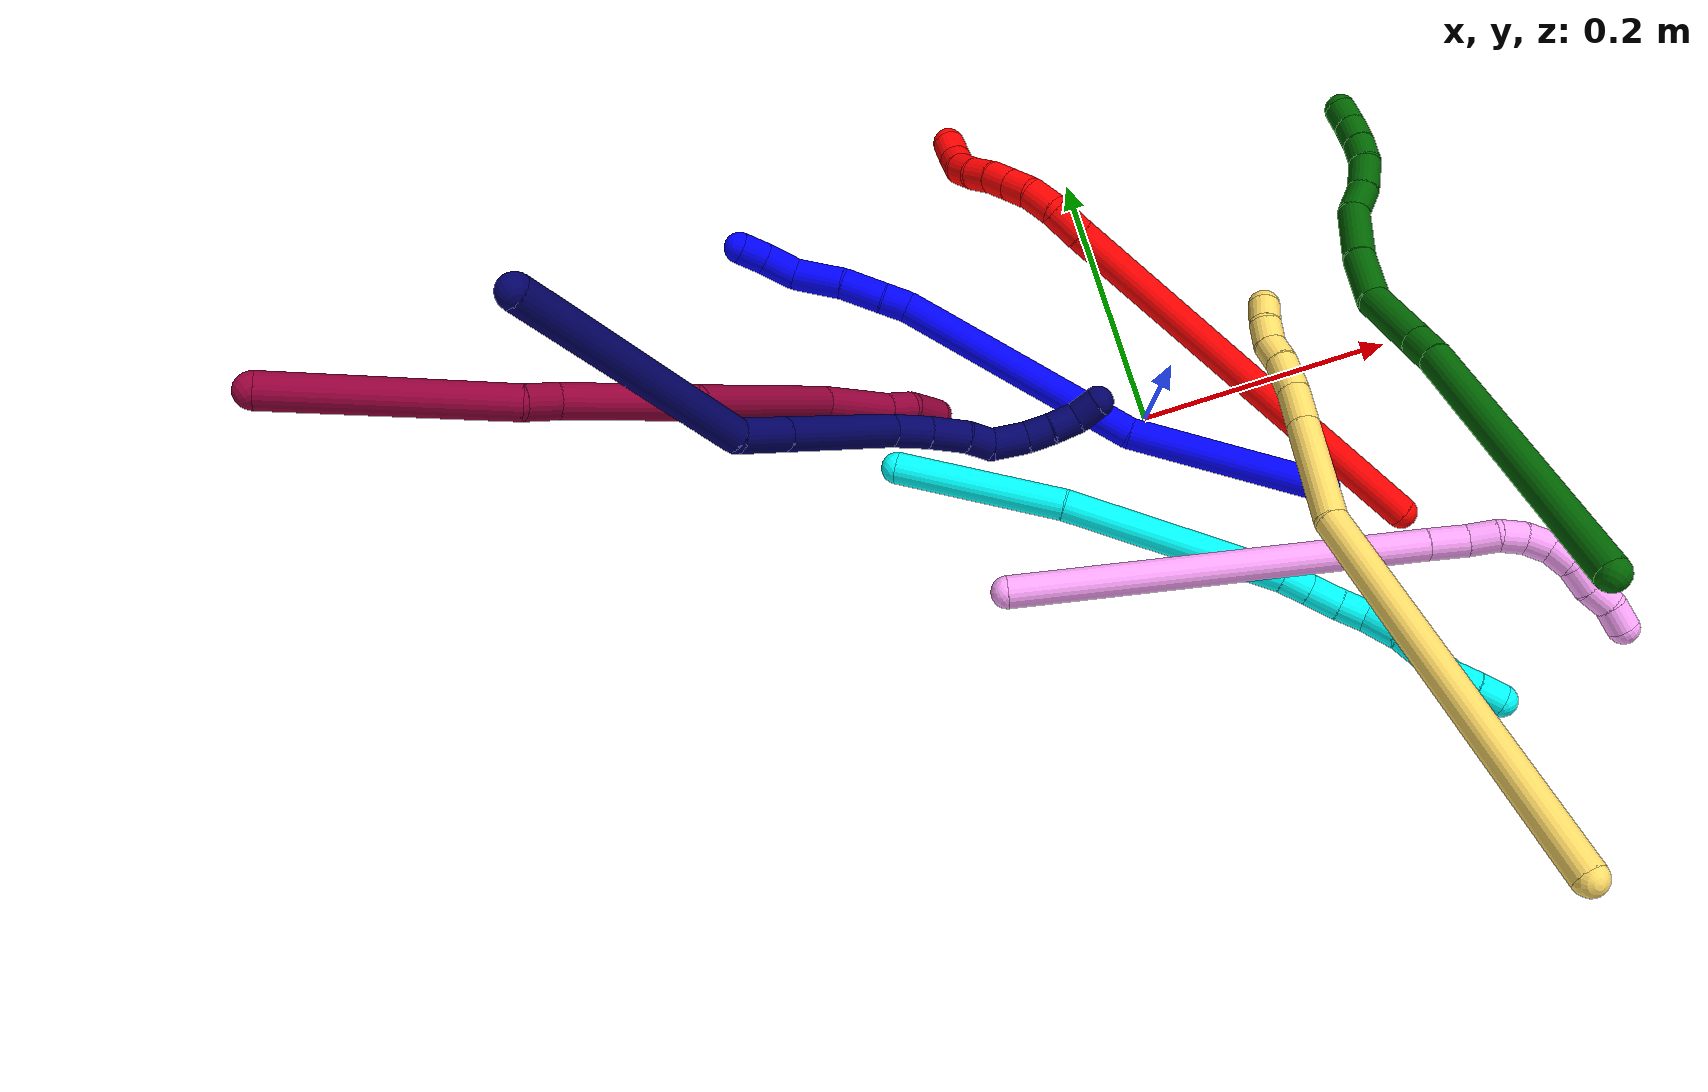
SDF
<sdf version="1.7">
 <world name="default">
  <plugin name="TubeGeneratorPlugin" filename="libtube_generator_plugin.so"/>
  <model name="photoneo_s_sensor">
   <static>1</static>
   <pose>0 0 2 1.57079 1.57079 3.14159</pose>
   <link name="link">
    <inertial><mass>0.1</mass></inertial>
    <sensor name="sensor" type="depth">
     <update_rate>30</update_rate>
     <camera>
      <horizontal_fov>1.22</horizontal_fov>
      <image><width>1920</width><height>1200</height><format>B8G8R8</format></image>
      <clip><near>0.1</near><far>4</far></clip>
      <depth_camera><output>points</output></depth_camera>
     </camera>
     <plugin name="camera_plugin" filename="libgazebo_ros_depth_camera.so">
      <baseline>0.2</baseline>
      <alwaysOn>1</alwaysOn>
      <updateRate>0.0</updateRate>
      <cameraName>camera_ir</cameraName>
      <imageTopicName>/camera/color/image_raw</imageTopicName>
      <cameraInfoTopicName>/camera/color/camera_info</cameraInfoTopicName>
      <depthImageTopicName>/camera/depth/image_raw</depthImageTopicName>
      <depthImageCameraInfoTopicName>/camera/depth/camera_info</depthImageCameraInfoTopicName>
      <pointCloudTopicName>/camera/depth/points</pointCloudTopicName>
      <frameName>fr_optical</frameName>
      <pointCloudCutoff>0.1</pointCloudCutoff>
      <pointCloudCutoffMax>2.0</pointCloudCutoffMax>
      <distortionK1>0</distortionK1>
      <distortionK2>0</distortionK2>
      <distortionK3>0</distortionK3>
      <distortionT1>0</distortionT1>
      <distortionT2>0</distortionT2>
      <CxPrime>0</CxPrime>
      <Cx>0</Cx>
      <Cy>0</Cy>
      <focalLength>0</focalLength>
      <hackBaseline>0</hackBaseline>
     </plugin>
    </sensor>
   </link>
  </model>
  <gravity>0 0 -9.8</gravity>
  <magnetic_field>6e-06 2.3e-05 -4.2e-05</magnetic_field>
  <atmosphere type="adiabatic"/>
  <physics name="default_physics" default="0" type="ode">
   <max_step_size>0.003</max_step_size>
   <real_time_factor>1</real_time_factor>
   <real_time_update_rate>1000</real_time_update_rate>
   <max_contacts>10000</max_contacts>
   <ode>
    <solver>
     <type>quick</type>
     <iters>100</iters>
     <sor>1.3</sor>
     <use_dynamic_moi_rescaling>0</use_dynamic_moi_rescaling>
    </solver>
    <constraints>
     <contact_max_correcting_vel>0</contact_max_correcting_vel>
     <contact_surface_layer>0.001</contact_surface_layer>
     <cfm>0</cfm>
     <erp>0.2</erp>
    </constraints>
   </ode>
  </physics>
  <scene><ambient>0.4 0.4 0.4 1</ambient><background>0.7 0.7 0.7 1</background><shadows>0</shadows></scene>
  <audio><device>default</device></audio>
  <spherical_coordinates>
   <surface_model>EARTH_WGS84</surface_model>
   <latitude_deg>0</latitude_deg>
   <longitude_deg>0</longitude_deg>
   <elevation>0</elevation>
   <heading_deg>0</heading_deg>
  </spherical_coordinates>
  <model name="bin">
   <static>1</static>
   <link name="bottom">
    <collision name="collision-bottom">
     <pose>0 0 -0.01 0 -0 0</pose>
     <geometry><box><size>0.8 0.6 0.02</size></box></geometry>
     <surface>
      <friction><ode><mu>100</mu><mu2>100</mu2></ode></friction>
      <contact><collide_bitmask>65535</collide_bitmask></contact>
     </surface>
    </collision>
   </link>
   <link name="west_wall">
    <collision name="collision-west_wall">
     <pose>-0.41 0 0.1 0 -0 0</pose>
     <geometry><box><size>0.02 0.6 0.2</size></box></geometry>
     <surface>
      <friction><ode><mu>100</mu><mu2>100</mu2></ode></friction>
      <contact><collide_bitmask>65535</collide_bitmask></contact>
     </surface>
    </collision>
   </link>
   <link name="east_wall">
    <collision name="collision-east_wall">
     <pose>0.41 0 0.1 0 -0 0</pose>
     <geometry><box><size>0.02 0.6 0.2</size></box></geometry>
     <surface>
      <friction><ode><mu>100</mu><mu2>100</mu2></ode></friction>
      <contact><collide_bitmask>65535</collide_bitmask></contact>
     </surface>
    </collision>
   </link>
   <link name="south_wall">
    <collision name="collision-south_wall">
     <pose>0 -0.31 0.1 0 -0 0</pose>
     <geometry><box><size>0.8 0.02 0.2</size></box></geometry>
     <surface>
      <friction><ode><mu>100</mu><mu2>100</mu2></ode></friction>
      <contact><collide_bitmask>65535</collide_bitmask></contact>
     </surface>
    </collision>
   </link>
   <link name="north_wall">
    <collision name="collision-north_wall">
     <pose>0 0.31 0.1 0 -0 0</pose>
     <geometry><box><size>0.8 0.02 0.2</size></box></geometry>
     <surface>
      <friction><ode><mu>100</mu><mu2>100</mu2></ode></friction>
      <contact><collide_bitmask>65535</collide_bitmask></contact>
     </surface>
    </collision>
   </link>
  </model>
  <model name="1">
   <static>0</static>
   <link name="1">
    <collision name="collision-cylinder-e_1_1_4">
     <pose>-0.045691 0.024071 0.05866 -0.389404 -0.624421 0.127128</pose>
     <geometry><cylinder><radius>0.0125</radius><length>0.156308</length></cylinder></geometry>
     <surface>
      <friction><ode><mu>1.16</mu><mu2>1.16</mu2><slip1>0</slip1><slip2>0</slip2></ode></friction>
      <contact><ode><kp>1e+06</kp><kd>1</kd><max_vel>0</max_vel><min_depth>0.001</min_depth></ode></contact>
     </surface>
    </collision>
    <visual name="visual-cylinder-e_1_1_4">
     <pose>-0.045691 0.024071 0.05866 -0.389404 -0.624421 0.127128</pose>
     <geometry><cylinder><radius>0.0125</radius><length>0.156308</length></cylinder></geometry>
     <material><ambient>0 0 1 1</ambient></material>
    </visual>
    <collision name="collision-cylinder-e_2_4_5">
     <pose>-0.140739 0.102122 0.18673 -0.660983 -0.511495 0.17893</pose>
     <geometry><cylinder><radius>0.0125</radius><length>0.201669</length></cylinder></geometry>
     <surface>
      <friction><ode><mu>1.16</mu><mu2>1.16</mu2><slip1>0</slip1><slip2>0</slip2></ode></friction>
      <contact><ode><kp>1e+06</kp><kd>1</kd><max_vel>0</max_vel><min_depth>0.001</min_depth></ode></contact>
     </surface>
    </collision>
    <visual name="visual-cylinder-e_2_4_5">
     <pose>-0.140739 0.102122 0.18673 -0.660983 -0.511495 0.17893</pose>
     <geometry><cylinder><radius>0.0125</radius><length>0.201669</length></cylinder></geometry>
     <material><ambient>0 0 1 1</ambient></material>
    </visual>
    <collision name="collision-cylinder-e_3_5_6">
     <pose>-0.194637 0.159531 0.26491 -0.372802 -0.449391 0.086153</pose>
     <geometry><cylinder><radius>0.0125</radius><length>0.020909</length></cylinder></geometry>
     <surface>
      <friction><ode><mu>1.16</mu><mu2>1.16</mu2><slip1>0</slip1><slip2>0</slip2></ode></friction>
      <contact><ode><kp>1e+06</kp><kd>1</kd><max_vel>0</max_vel><min_depth>0.001</min_depth></ode></contact>
     </surface>
    </collision>
    <visual name="visual-cylinder-e_3_5_6">
     <pose>-0.194637 0.159531 0.26491 -0.372802 -0.449391 0.086153</pose>
     <geometry><cylinder><radius>0.0125</radius><length>0.020909</length></cylinder></geometry>
     <material><ambient>0 0 1 1</ambient></material>
    </visual>
    <collision name="collision-cylinder-e_4_6_7">
     <pose>-0.207949 0.16921 0.286517 -0.453001 -0.55083 0.130068</pose>
     <geometry><cylinder><radius>0.0125</radius><length>0.033511</length></cylinder></geometry>
     <surface>
      <friction><ode><mu>1.16</mu><mu2>1.16</mu2><slip1>0</slip1><slip2>0</slip2></ode></friction>
      <contact><ode><kp>1e+06</kp><kd>1</kd><max_vel>0</max_vel><min_depth>0.001</min_depth></ode></contact>
     </surface>
    </collision>
    <visual name="visual-cylinder-e_4_6_7">
     <pose>-0.207949 0.16921 0.286517 -0.453001 -0.55083 0.130068</pose>
     <geometry><cylinder><radius>0.0125</radius><length>0.033511</length></cylinder></geometry>
     <material><ambient>0 0 1 1</ambient></material>
    </visual>
    <collision name="collision-cylinder-e_5_7_8">
     <pose>-0.229751 0.180787 0.313221 -0.366902 -0.720155 0.13948</pose>
     <geometry><cylinder><radius>0.0125</radius><length>0.039523</length></cylinder></geometry>
     <surface>
      <friction><ode><mu>1.16</mu><mu2>1.16</mu2><slip1>0</slip1><slip2>0</slip2></ode></friction>
      <contact><ode><kp>1e+06</kp><kd>1</kd><max_vel>0</max_vel><min_depth>0.001</min_depth></ode></contact>
     </surface>
    </collision>
    <visual name="visual-cylinder-e_5_7_8">
     <pose>-0.229751 0.180787 0.313221 -0.366902 -0.720155 0.13948</pose>
     <geometry><cylinder><radius>0.0125</radius><length>0.039523</length></cylinder></geometry>
     <material><ambient>0 0 1 1</ambient></material>
    </visual>
    <collision name="collision-cylinder-e_6_8_9">
     <pose>-0.246078 0.191148 0.339198 -0.393814 -0.246081 0.04933</pose>
     <geometry><cylinder><radius>0.0125</radius><length>0.027045</length></cylinder></geometry>
     <surface>
      <friction><ode><mu>1.16</mu><mu2>1.16</mu2><slip1>0</slip1><slip2>0</slip2></ode></friction>
      <contact><ode><kp>1e+06</kp><kd>1</kd><max_vel>0</max_vel><min_depth>0.001</min_depth></ode></contact>
     </surface>
    </collision>
    <visual name="visual-cylinder-e_6_8_9">
     <pose>-0.246078 0.191148 0.339198 -0.393814 -0.246081 0.04933</pose>
     <geometry><cylinder><radius>0.0125</radius><length>0.027045</length></cylinder></geometry>
     <material><ambient>0 0 1 1</ambient></material>
    </visual>
    <collision name="collision-cylinder-e_7_9_2">
     <pose>-0.25132 0.199037 0.361242 -0.27999 -0.186273 0.026324</pose>
     <geometry><cylinder><radius>0.0125</radius><length>0.021033</length></cylinder></geometry>
     <surface>
      <friction><ode><mu>1.16</mu><mu2>1.16</mu2><slip1>0</slip1><slip2>0</slip2></ode></friction>
      <contact><ode><kp>1e+06</kp><kd>1</kd><max_vel>0</max_vel><min_depth>0.001</min_depth></ode></contact>
     </surface>
    </collision>
    <visual name="visual-cylinder-e_7_9_2">
     <pose>-0.25132 0.199037 0.361242 -0.27999 -0.186273 0.026324</pose>
     <geometry><cylinder><radius>0.0125</radius><length>0.021033</length></cylinder></geometry>
     <material><ambient>0 0 1 1</ambient></material>
    </visual>
    <collision name="collision-sphere-2">
     <pose>-0.253268 0.201893 0.371174 0 -0 0</pose>
     <geometry><sphere><radius>0.0125</radius></sphere></geometry>
     <surface>
      <friction><ode><mu>1.16</mu><mu2>1.16</mu2><slip1>0</slip1><slip2>0</slip2></ode></friction>
      <contact><ode><kp>1e+06</kp><kd>1</kd><max_vel>0</max_vel><min_depth>0.001</min_depth></ode></contact>
     </surface>
    </collision>
    <visual name="visual-sphere-2">
     <pose>-0.253268 0.201893 0.371174 0 -0 0</pose>
     <geometry><sphere><radius>0.0125</radius></sphere></geometry>
     <material><ambient>0 0 1 1</ambient></material>
    </visual>
    <collision name="collision-sphere-9">
     <pose>-0.249373 0.196181 0.35131 0 -0 0</pose>
     <geometry><sphere><radius>0.0125</radius></sphere></geometry>
     <surface>
      <friction><ode><mu>1.16</mu><mu2>1.16</mu2><slip1>0</slip1><slip2>0</slip2></ode></friction>
      <contact><ode><kp>1e+06</kp><kd>1</kd><max_vel>0</max_vel><min_depth>0.001</min_depth></ode></contact>
     </surface>
    </collision>
    <visual name="visual-sphere-9">
     <pose>-0.249373 0.196181 0.35131 0 -0 0</pose>
     <geometry><sphere><radius>0.0125</radius></sphere></geometry>
     <material><ambient>0 0 1 1</ambient></material>
    </visual>
    <collision name="collision-sphere-4">
     <pose>-0.091382 0.048143 0.117319 0 -0 0</pose>
     <geometry><sphere><radius>0.0125</radius></sphere></geometry>
     <surface>
      <friction><ode><mu>1.16</mu><mu2>1.16</mu2><slip1>0</slip1><slip2>0</slip2></ode></friction>
      <contact><ode><kp>1e+06</kp><kd>1</kd><max_vel>0</max_vel><min_depth>0.001</min_depth></ode></contact>
     </surface>
    </collision>
    <visual name="visual-sphere-4">
     <pose>-0.091382 0.048143 0.117319 0 -0 0</pose>
     <geometry><sphere><radius>0.0125</radius></sphere></geometry>
     <material><ambient>0 0 1 1</ambient></material>
    </visual>
    <collision name="collision-sphere-1">
     <geometry><sphere><radius>0.0125</radius></sphere></geometry>
     <surface>
      <friction><ode><mu>1.16</mu><mu2>1.16</mu2><slip1>0</slip1><slip2>0</slip2></ode></friction>
      <contact><ode><kp>1e+06</kp><kd>1</kd><max_vel>0</max_vel><min_depth>0.001</min_depth></ode></contact>
     </surface>
    </collision>
    <visual name="visual-sphere-1">
     <geometry><sphere><radius>0.0125</radius></sphere></geometry>
     <material><ambient>0 0 1 1</ambient></material>
    </visual>
    <collision name="collision-sphere-8">
     <pose>-0.242784 0.186116 0.327087 0 -0 0</pose>
     <geometry><sphere><radius>0.0125</radius></sphere></geometry>
     <surface>
      <friction><ode><mu>1.16</mu><mu2>1.16</mu2><slip1>0</slip1><slip2>0</slip2></ode></friction>
      <contact><ode><kp>1e+06</kp><kd>1</kd><max_vel>0</max_vel><min_depth>0.001</min_depth></ode></contact>
     </surface>
    </collision>
    <visual name="visual-sphere-8">
     <pose>-0.242784 0.186116 0.327087 0 -0 0</pose>
     <geometry><sphere><radius>0.0125</radius></sphere></geometry>
     <material><ambient>0 0 1 1</ambient></material>
    </visual>
    <collision name="collision-sphere-5">
     <pose>-0.190095 0.156101 0.25614 0 -0 0</pose>
     <geometry><sphere><radius>0.0125</radius></sphere></geometry>
     <surface>
      <friction><ode><mu>1.16</mu><mu2>1.16</mu2><slip1>0</slip1><slip2>0</slip2></ode></friction>
      <contact><ode><kp>1e+06</kp><kd>1</kd><max_vel>0</max_vel><min_depth>0.001</min_depth></ode></contact>
     </surface>
    </collision>
    <visual name="visual-sphere-5">
     <pose>-0.190095 0.156101 0.25614 0 -0 0</pose>
     <geometry><sphere><radius>0.0125</radius></sphere></geometry>
     <material><ambient>0 0 1 1</ambient></material>
    </visual>
    <collision name="collision-sphere-6">
     <pose>-0.199179 0.162961 0.27368 0 -0 0</pose>
     <geometry><sphere><radius>0.0125</radius></sphere></geometry>
     <surface>
      <friction><ode><mu>1.16</mu><mu2>1.16</mu2><slip1>0</slip1><slip2>0</slip2></ode></friction>
      <contact><ode><kp>1e+06</kp><kd>1</kd><max_vel>0</max_vel><min_depth>0.001</min_depth></ode></contact>
     </surface>
    </collision>
    <visual name="visual-sphere-6">
     <pose>-0.199179 0.162961 0.27368 0 -0 0</pose>
     <geometry><sphere><radius>0.0125</radius></sphere></geometry>
     <material><ambient>0 0 1 1</ambient></material>
    </visual>
    <collision name="collision-sphere-7">
     <pose>-0.216718 0.175458 0.299354 0 -0 0</pose>
     <geometry><sphere><radius>0.0125</radius></sphere></geometry>
     <surface>
      <friction><ode><mu>1.16</mu><mu2>1.16</mu2><slip1>0</slip1><slip2>0</slip2></ode></friction>
      <contact><ode><kp>1e+06</kp><kd>1</kd><max_vel>0</max_vel><min_depth>0.001</min_depth></ode></contact>
     </surface>
    </collision>
    <visual name="visual-sphere-7">
     <pose>-0.216718 0.175458 0.299354 0 -0 0</pose>
     <geometry><sphere><radius>0.0125</radius></sphere></geometry>
     <material><ambient>0 0 1 1</ambient></material>
    </visual>
    <inertial>
     <pose>-0.13517 0.09973 0.182237 0 -0 0</pose>
     <mass>0.5</mass>
     <inertia><ixx>0.000991</ixx><ixy>0</ixy><ixz>0</ixz><iyy>0.001055</iyy><iyz>0</iyz><izz>9e-05</izz></inertia>
    </inertial>
   </link>
   <pose>0.114183 -0.094349 0.012635 -0.179534 -0.871286 -0.127304</pose>
  </model>
  <model name="2">
   <static>0</static>
   <link name="2">
    <collision name="collision-cylinder-e_1_1_4">
     <pose>-0.092895 0.13589 -0.008558 -1.63369 -0.598713 0.635111</pose>
     <geometry><cylinder><radius>0.0125</radius><length>0.32966</length></cylinder></geometry>
     <surface>
      <friction><ode><mu>1.16</mu><mu2>1.16</mu2><slip1>0</slip1><slip2>0</slip2></ode></friction>
      <contact><ode><kp>1e+06</kp><kd>1</kd><max_vel>0</max_vel><min_depth>0.001</min_depth></ode></contact>
     </surface>
    </collision>
    <visual name="visual-cylinder-e_1_1_4">
     <pose>-0.092895 0.13589 -0.008558 -1.63369 -0.598713 0.635111</pose>
     <geometry><cylinder><radius>0.0125</radius><length>0.32966</length></cylinder></geometry>
     <material><ambient>1 0 0 1</ambient></material>
    </visual>
    <collision name="collision-cylinder-e_2_4_5">
     <pose>-0.19285 0.282997 -0.017759 -1.62815 -0.561037 0.592321</pose>
     <geometry><cylinder><radius>0.0125</radius><length>0.026538</length></cylinder></geometry>
     <surface>
      <friction><ode><mu>1.16</mu><mu2>1.16</mu2><slip1>0</slip1><slip2>0</slip2></ode></friction>
      <contact><ode><kp>1e+06</kp><kd>1</kd><max_vel>0</max_vel><min_depth>0.001</min_depth></ode></contact>
     </surface>
    </collision>
    <visual name="visual-cylinder-e_2_4_5">
     <pose>-0.19285 0.282997 -0.017759 -1.62815 -0.561037 0.592321</pose>
     <geometry><cylinder><radius>0.0125</radius><length>0.026538</length></cylinder></geometry>
     <material><ambient>1 0 0 1</ambient></material>
    </visual>
    <collision name="collision-cylinder-e_3_5_6">
     <pose>-0.205943 0.302505 -0.024125 -2.17489 -0.539646 0.969894</pose>
     <geometry><cylinder><radius>0.0125</radius><length>0.023486</length></cylinder></geometry>
     <surface>
      <friction><ode><mu>1.16</mu><mu2>1.16</mu2><slip1>0</slip1><slip2>0</slip2></ode></friction>
      <contact><ode><kp>1e+06</kp><kd>1</kd><max_vel>0</max_vel><min_depth>0.001</min_depth></ode></contact>
     </surface>
    </collision>
    <visual name="visual-cylinder-e_3_5_6">
     <pose>-0.205943 0.302505 -0.024125 -2.17489 -0.539646 0.969894</pose>
     <geometry><cylinder><radius>0.0125</radius><length>0.023486</length></cylinder></geometry>
     <material><ambient>1 0 0 1</ambient></material>
    </visual>
    <collision name="collision-cylinder-e_4_6_7">
     <pose>-0.217566 0.315826 -0.036661 -2.50567 -0.583335 1.47903</pose>
     <geometry><cylinder><radius>0.0125</radius><length>0.020294</length></cylinder></geometry>
     <surface>
      <friction><ode><mu>1.16</mu><mu2>1.16</mu2><slip1>0</slip1><slip2>0</slip2></ode></friction>
      <contact><ode><kp>1e+06</kp><kd>1</kd><max_vel>0</max_vel><min_depth>0.001</min_depth></ode></contact>
     </surface>
    </collision>
    <visual name="visual-cylinder-e_4_6_7">
     <pose>-0.217566 0.315826 -0.036661 -2.50567 -0.583335 1.47903</pose>
     <geometry><cylinder><radius>0.0125</radius><length>0.020294</length></cylinder></geometry>
     <material><ambient>1 0 0 1</ambient></material>
    </visual>
    <collision name="collision-cylinder-e_5_7_8">
     <pose>-0.228619 0.32574 -0.050294 -2.52005 -0.577308 1.49243</pose>
     <geometry><cylinder><radius>0.0125</radius><length>0.02002</length></cylinder></geometry>
     <surface>
      <friction><ode><mu>1.16</mu><mu2>1.16</mu2><slip1>0</slip1><slip2>0</slip2></ode></friction>
      <contact><ode><kp>1e+06</kp><kd>1</kd><max_vel>0</max_vel><min_depth>0.001</min_depth></ode></contact>
     </surface>
    </collision>
    <visual name="visual-cylinder-e_5_7_8">
     <pose>-0.228619 0.32574 -0.050294 -2.52005 -0.577308 1.49243</pose>
     <geometry><cylinder><radius>0.0125</radius><length>0.02002</length></cylinder></geometry>
     <material><ambient>1 0 0 1</ambient></material>
    </visual>
    <collision name="collision-cylinder-e_6_8_9">
     <pose>-0.239961 0.333999 -0.064465 -2.71121 -0.628417 1.95741</pose>
     <geometry><cylinder><radius>0.0125</radius><length>0.020001</length></cylinder></geometry>
     <surface>
      <friction><ode><mu>1.16</mu><mu2>1.16</mu2><slip1>0</slip1><slip2>0</slip2></ode></friction>
      <contact><ode><kp>1e+06</kp><kd>1</kd><max_vel>0</max_vel><min_depth>0.001</min_depth></ode></contact>
     </surface>
    </collision>
    <visual name="visual-cylinder-e_6_8_9">
     <pose>-0.239961 0.333999 -0.064465 -2.71121 -0.628417 1.95741</pose>
     <geometry><cylinder><radius>0.0125</radius><length>0.020001</length></cylinder></geometry>
     <material><ambient>1 0 0 1</ambient></material>
    </visual>
    <collision name="collision-cylinder-e_7_9_10">
     <pose>-0.249487 0.340876 -0.080445 -2.75609 -0.373338 1.53797</pose>
     <geometry><cylinder><radius>0.0125</radius><length>0.02</length></cylinder></geometry>
     <surface>
      <friction><ode><mu>1.16</mu><mu2>1.16</mu2><slip1>0</slip1><slip2>0</slip2></ode></friction>
      <contact><ode><kp>1e+06</kp><kd>1</kd><max_vel>0</max_vel><min_depth>0.001</min_depth></ode></contact>
     </surface>
    </collision>
    <visual name="visual-cylinder-e_7_9_10">
     <pose>-0.249487 0.340876 -0.080445 -2.75609 -0.373338 1.53797</pose>
     <geometry><cylinder><radius>0.0125</radius><length>0.02</length></cylinder></geometry>
     <material><ambient>1 0 0 1</ambient></material>
    </visual>
    <collision name="collision-cylinder-e_8_10_11">
     <pose>-0.253103 0.348627 -0.098126 -2.70272 0.003173 -0.014227</pose>
     <geometry><cylinder><radius>0.0125</radius><length>0.020001</length></cylinder></geometry>
     <surface>
      <friction><ode><mu>1.16</mu><mu2>1.16</mu2><slip1>0</slip1><slip2>0</slip2></ode></friction>
      <contact><ode><kp>1e+06</kp><kd>1</kd><max_vel>0</max_vel><min_depth>0.001</min_depth></ode></contact>
     </surface>
    </collision>
    <visual name="visual-cylinder-e_8_10_11">
     <pose>-0.253103 0.348627 -0.098126 -2.70272 0.003173 -0.014227</pose>
     <geometry><cylinder><radius>0.0125</radius><length>0.020001</length></cylinder></geometry>
     <material><ambient>1 0 0 1</ambient></material>
    </visual>
    <collision name="collision-cylinder-e_9_11_2">
     <pose>-0.25349 0.359837 -0.114346 -2.37087 -0.041908 0.103236</pose>
     <geometry><cylinder><radius>0.0125</radius><length>0.02</length></cylinder></geometry>
     <surface>
      <friction><ode><mu>1.16</mu><mu2>1.16</mu2><slip1>0</slip1><slip2>0</slip2></ode></friction>
      <contact><ode><kp>1e+06</kp><kd>1</kd><max_vel>0</max_vel><min_depth>0.001</min_depth></ode></contact>
     </surface>
    </collision>
    <visual name="visual-cylinder-e_9_11_2">
     <pose>-0.25349 0.359837 -0.114346 -2.37087 -0.041908 0.103236</pose>
     <geometry><cylinder><radius>0.0125</radius><length>0.02</length></cylinder></geometry>
     <material><ambient>1 0 0 1</ambient></material>
    </visual>
    <collision name="collision-sphere-2">
     <pose>-0.253909 0.366797 -0.121514 0 -0 0</pose>
     <geometry><sphere><radius>0.0125</radius></sphere></geometry>
     <surface>
      <friction><ode><mu>1.16</mu><mu2>1.16</mu2><slip1>0</slip1><slip2>0</slip2></ode></friction>
      <contact><ode><kp>1e+06</kp><kd>1</kd><max_vel>0</max_vel><min_depth>0.001</min_depth></ode></contact>
     </surface>
    </collision>
    <visual name="visual-sphere-2">
     <pose>-0.253909 0.366797 -0.121514 0 -0 0</pose>
     <geometry><sphere><radius>0.0125</radius></sphere></geometry>
     <material><ambient>1 0 0 1</ambient></material>
    </visual>
    <collision name="collision-sphere-11">
     <pose>-0.253071 0.352876 -0.107178 0 -0 0</pose>
     <geometry><sphere><radius>0.0125</radius></sphere></geometry>
     <surface>
      <friction><ode><mu>1.16</mu><mu2>1.16</mu2><slip1>0</slip1><slip2>0</slip2></ode></friction>
      <contact><ode><kp>1e+06</kp><kd>1</kd><max_vel>0</max_vel><min_depth>0.001</min_depth></ode></contact>
     </surface>
    </collision>
    <visual name="visual-sphere-11">
     <pose>-0.253071 0.352876 -0.107178 0 -0 0</pose>
     <geometry><sphere><radius>0.0125</radius></sphere></geometry>
     <material><ambient>1 0 0 1</ambient></material>
    </visual>
    <collision name="collision-sphere-10">
     <pose>-0.253134 0.344377 -0.089073 0 -0 0</pose>
     <geometry><sphere><radius>0.0125</radius></sphere></geometry>
     <surface>
      <friction><ode><mu>1.16</mu><mu2>1.16</mu2><slip1>0</slip1><slip2>0</slip2></ode></friction>
      <contact><ode><kp>1e+06</kp><kd>1</kd><max_vel>0</max_vel><min_depth>0.001</min_depth></ode></contact>
     </surface>
    </collision>
    <visual name="visual-sphere-10">
     <pose>-0.253134 0.344377 -0.089073 0 -0 0</pose>
     <geometry><sphere><radius>0.0125</radius></sphere></geometry>
     <material><ambient>1 0 0 1</ambient></material>
    </visual>
    <collision name="collision-sphere-9">
     <pose>-0.24584 0.337375 -0.071817 0 -0 0</pose>
     <geometry><sphere><radius>0.0125</radius></sphere></geometry>
     <surface>
      <friction><ode><mu>1.16</mu><mu2>1.16</mu2><slip1>0</slip1><slip2>0</slip2></ode></friction>
      <contact><ode><kp>1e+06</kp><kd>1</kd><max_vel>0</max_vel><min_depth>0.001</min_depth></ode></contact>
     </surface>
    </collision>
    <visual name="visual-sphere-9">
     <pose>-0.24584 0.337375 -0.071817 0 -0 0</pose>
     <geometry><sphere><radius>0.0125</radius></sphere></geometry>
     <material><ambient>1 0 0 1</ambient></material>
    </visual>
    <collision name="collision-sphere-4">
     <pose>-0.18579 0.271781 -0.017115 0 -0 0</pose>
     <geometry><sphere><radius>0.0125</radius></sphere></geometry>
     <surface>
      <friction><ode><mu>1.16</mu><mu2>1.16</mu2><slip1>0</slip1><slip2>0</slip2></ode></friction>
      <contact><ode><kp>1e+06</kp><kd>1</kd><max_vel>0</max_vel><min_depth>0.001</min_depth></ode></contact>
     </surface>
    </collision>
    <visual name="visual-sphere-4">
     <pose>-0.18579 0.271781 -0.017115 0 -0 0</pose>
     <geometry><sphere><radius>0.0125</radius></sphere></geometry>
     <material><ambient>1 0 0 1</ambient></material>
    </visual>
    <collision name="collision-sphere-1">
     <geometry><sphere><radius>0.0125</radius></sphere></geometry>
     <surface>
      <friction><ode><mu>1.16</mu><mu2>1.16</mu2><slip1>0</slip1><slip2>0</slip2></ode></friction>
      <contact><ode><kp>1e+06</kp><kd>1</kd><max_vel>0</max_vel><min_depth>0.001</min_depth></ode></contact>
     </surface>
    </collision>
    <visual name="visual-sphere-1">
     <geometry><sphere><radius>0.0125</radius></sphere></geometry>
     <material><ambient>1 0 0 1</ambient></material>
    </visual>
    <collision name="collision-sphere-8">
     <pose>-0.234082 0.330624 -0.057113 0 -0 0</pose>
     <geometry><sphere><radius>0.0125</radius></sphere></geometry>
     <surface>
      <friction><ode><mu>1.16</mu><mu2>1.16</mu2><slip1>0</slip1><slip2>0</slip2></ode></friction>
      <contact><ode><kp>1e+06</kp><kd>1</kd><max_vel>0</max_vel><min_depth>0.001</min_depth></ode></contact>
     </surface>
    </collision>
    <visual name="visual-sphere-8">
     <pose>-0.234082 0.330624 -0.057113 0 -0 0</pose>
     <geometry><sphere><radius>0.0125</radius></sphere></geometry>
     <material><ambient>1 0 0 1</ambient></material>
    </visual>
    <collision name="collision-sphere-5">
     <pose>-0.19991 0.294214 -0.018403 0 -0 0</pose>
     <geometry><sphere><radius>0.0125</radius></sphere></geometry>
     <surface>
      <friction><ode><mu>1.16</mu><mu2>1.16</mu2><slip1>0</slip1><slip2>0</slip2></ode></friction>
      <contact><ode><kp>1e+06</kp><kd>1</kd><max_vel>0</max_vel><min_depth>0.001</min_depth></ode></contact>
     </surface>
    </collision>
    <visual name="visual-sphere-5">
     <pose>-0.19991 0.294214 -0.018403 0 -0 0</pose>
     <geometry><sphere><radius>0.0125</radius></sphere></geometry>
     <material><ambient>1 0 0 1</ambient></material>
    </visual>
    <collision name="collision-sphere-6">
     <pose>-0.211977 0.310796 -0.029848 0 -0 0</pose>
     <geometry><sphere><radius>0.0125</radius></sphere></geometry>
     <surface>
      <friction><ode><mu>1.16</mu><mu2>1.16</mu2><slip1>0</slip1><slip2>0</slip2></ode></friction>
      <contact><ode><kp>1e+06</kp><kd>1</kd><max_vel>0</max_vel><min_depth>0.001</min_depth></ode></contact>
     </surface>
    </collision>
    <visual name="visual-sphere-6">
     <pose>-0.211977 0.310796 -0.029848 0 -0 0</pose>
     <geometry><sphere><radius>0.0125</radius></sphere></geometry>
     <material><ambient>1 0 0 1</ambient></material>
    </visual>
    <collision name="collision-sphere-7">
     <pose>-0.223155 0.320856 -0.043475 0 -0 0</pose>
     <geometry><sphere><radius>0.0125</radius></sphere></geometry>
     <surface>
      <friction><ode><mu>1.16</mu><mu2>1.16</mu2><slip1>0</slip1><slip2>0</slip2></ode></friction>
      <contact><ode><kp>1e+06</kp><kd>1</kd><max_vel>0</max_vel><min_depth>0.001</min_depth></ode></contact>
     </surface>
    </collision>
    <visual name="visual-sphere-7">
     <pose>-0.223155 0.320856 -0.043475 0 -0 0</pose>
     <geometry><sphere><radius>0.0125</radius></sphere></geometry>
     <material><ambient>1 0 0 1</ambient></material>
    </visual>
    <inertial>
     <pose>-0.138984 0.200021 -0.025515 0 -0 0</pose>
     <mass>0.5</mass>
     <inertia>
      <ixx>0.003457</ixx>
      <ixy>0</ixy>
      <ixz>0</ixz>
      <iyy>0.002355</iyy>
      <iyz>0</iyz>
      <izz>-0.000794</izz>
     </inertia>
    </inertial>
   </link>
   <pose>0.164917 -0.131739 0.011496 0.297833 0.033577 -0.021047</pose>
  </model>
  <model name="3">
   <static>0</static>
   <link name="3">
    <collision name="collision-cylinder-e_1_1_4">
     <pose>0.041399 -0.029282 0.043448 0.593027 0.668701 0.211479</pose>
     <geometry><cylinder><radius>0.0125</radius><length>0.133551</length></cylinder></geometry>
     <surface>
      <friction><ode><mu>1.16</mu><mu2>1.16</mu2><slip1>0</slip1><slip2>0</slip2></ode></friction>
      <contact><ode><kp>1e+06</kp><kd>1</kd><max_vel>0</max_vel><min_depth>0.001</min_depth></ode></contact>
     </surface>
    </collision>
    <visual name="visual-cylinder-e_1_1_4">
     <pose>0.041399 -0.029282 0.043448 0.593027 0.668701 0.211479</pose>
     <geometry><cylinder><radius>0.0125</radius><length>0.133551</length></cylinder></geometry>
     <material><ambient>0.003922 1 0.996078 1</ambient></material>
    </visual>
    <collision name="collision-cylinder-e_2_4_5">
     <pose>0.144942 -0.088887 0.141372 0.507932 0.783761 0.21372</pose>
     <geometry><cylinder><radius>0.0125</radius><length>0.176058</length></cylinder></geometry>
     <surface>
      <friction><ode><mu>1.16</mu><mu2>1.16</mu2><slip1>0</slip1><slip2>0</slip2></ode></friction>
      <contact><ode><kp>1e+06</kp><kd>1</kd><max_vel>0</max_vel><min_depth>0.001</min_depth></ode></contact>
     </surface>
    </collision>
    <visual name="visual-cylinder-e_2_4_5">
     <pose>0.144942 -0.088887 0.141372 0.507932 0.783761 0.21372</pose>
     <geometry><cylinder><radius>0.0125</radius><length>0.176058</length></cylinder></geometry>
     <material><ambient>0.003922 1 0.996078 1</ambient></material>
    </visual>
    <collision name="collision-cylinder-e_3_5_6">
     <pose>0.216009 -0.122437 0.20179 0.497442 0.922474 0.251123</pose>
     <geometry><cylinder><radius>0.0125</radius><length>0.022389</length></cylinder></geometry>
     <surface>
      <friction><ode><mu>1.16</mu><mu2>1.16</mu2><slip1>0</slip1><slip2>0</slip2></ode></friction>
      <contact><ode><kp>1e+06</kp><kd>1</kd><max_vel>0</max_vel><min_depth>0.001</min_depth></ode></contact>
     </surface>
    </collision>
    <visual name="visual-cylinder-e_3_5_6">
     <pose>0.216009 -0.122437 0.20179 0.497442 0.922474 0.251123</pose>
     <geometry><cylinder><radius>0.0125</radius><length>0.022389</length></cylinder></geometry>
     <material><ambient>0.003922 1 0.996078 1</ambient></material>
    </visual>
    <collision name="collision-cylinder-e_4_6_7">
     <pose>0.23556 -0.12954 0.21474 0.505208 0.924923 0.255946</pose>
     <geometry><cylinder><radius>0.0125</radius><length>0.026616</length></cylinder></geometry>
     <surface>
      <friction><ode><mu>1.16</mu><mu2>1.16</mu2><slip1>0</slip1><slip2>0</slip2></ode></friction>
      <contact><ode><kp>1e+06</kp><kd>1</kd><max_vel>0</max_vel><min_depth>0.001</min_depth></ode></contact>
     </surface>
    </collision>
    <visual name="visual-cylinder-e_4_6_7">
     <pose>0.23556 -0.12954 0.21474 0.505208 0.924923 0.255946</pose>
     <geometry><cylinder><radius>0.0125</radius><length>0.026616</length></cylinder></geometry>
     <material><ambient>0.003922 1 0.996078 1</ambient></material>
    </visual>
    <collision name="collision-cylinder-e_5_7_8">
     <pose>0.254836 -0.138997 0.227447 0.774963 0.825925 0.353897</pose>
     <geometry><cylinder><radius>0.0125</radius><length>0.02353</length></cylinder></geometry>
     <surface>
      <friction><ode><mu>1.16</mu><mu2>1.16</mu2><slip1>0</slip1><slip2>0</slip2></ode></friction>
      <contact><ode><kp>1e+06</kp><kd>1</kd><max_vel>0</max_vel><min_depth>0.001</min_depth></ode></contact>
     </surface>
    </collision>
    <visual name="visual-cylinder-e_5_7_8">
     <pose>0.254836 -0.138997 0.227447 0.774963 0.825925 0.353897</pose>
     <geometry><cylinder><radius>0.0125</radius><length>0.02353</length></cylinder></geometry>
     <material><ambient>0.003922 1 0.996078 1</ambient></material>
    </visual>
    <collision name="collision-cylinder-e_6_8_9">
     <pose>0.272626 -0.155858 0.235717 1.34657 0.668592 0.540519</pose>
     <geometry><cylinder><radius>0.0125</radius><length>0.029492</length></cylinder></geometry>
     <surface>
      <friction><ode><mu>1.16</mu><mu2>1.16</mu2><slip1>0</slip1><slip2>0</slip2></ode></friction>
      <contact><ode><kp>1e+06</kp><kd>1</kd><max_vel>0</max_vel><min_depth>0.001</min_depth></ode></contact>
     </surface>
    </collision>
    <visual name="visual-cylinder-e_6_8_9">
     <pose>0.272626 -0.155858 0.235717 1.34657 0.668592 0.540519</pose>
     <geometry><cylinder><radius>0.0125</radius><length>0.029492</length></cylinder></geometry>
     <material><ambient>0.003922 1 0.996078 1</ambient></material>
    </visual>
    <collision name="collision-cylinder-e_7_9_10">
     <pose>0.292516 -0.172763 0.241053 1.11413 1.04308 0.687399</pose>
     <geometry><cylinder><radius>0.0125</radius><length>0.024883</length></cylinder></geometry>
     <surface>
      <friction><ode><mu>1.16</mu><mu2>1.16</mu2><slip1>0</slip1><slip2>0</slip2></ode></friction>
      <contact><ode><kp>1e+06</kp><kd>1</kd><max_vel>0</max_vel><min_depth>0.001</min_depth></ode></contact>
     </surface>
    </collision>
    <visual name="visual-cylinder-e_7_9_10">
     <pose>0.292516 -0.172763 0.241053 1.11413 1.04308 0.687399</pose>
     <geometry><cylinder><radius>0.0125</radius><length>0.024883</length></cylinder></geometry>
     <material><ambient>0.003922 1 0.996078 1</ambient></material>
    </visual>
    <collision name="collision-cylinder-e_8_10_11">
     <pose>0.312894 -0.182943 0.246119 1.10288 1.08322 0.708844</pose>
     <geometry><cylinder><radius>0.0125</radius><length>0.021799</length></cylinder></geometry>
     <surface>
      <friction><ode><mu>1.16</mu><mu2>1.16</mu2><slip1>0</slip1><slip2>0</slip2></ode></friction>
      <contact><ode><kp>1e+06</kp><kd>1</kd><max_vel>0</max_vel><min_depth>0.001</min_depth></ode></contact>
     </surface>
    </collision>
    <visual name="visual-cylinder-e_8_10_11">
     <pose>0.312894 -0.182943 0.246119 1.10288 1.08322 0.708844</pose>
     <geometry><cylinder><radius>0.0125</radius><length>0.021799</length></cylinder></geometry>
     <material><ambient>0.003922 1 0.996078 1</ambient></material>
    </visual>
    <collision name="collision-cylinder-e_9_11_12">
     <pose>0.330412 -0.191022 0.253747 0.584268 0.890402 0.285048</pose>
     <geometry><cylinder><radius>0.0125</radius><length>0.020296</length></cylinder></geometry>
     <surface>
      <friction><ode><mu>1.16</mu><mu2>1.16</mu2><slip1>0</slip1><slip2>0</slip2></ode></friction>
      <contact><ode><kp>1e+06</kp><kd>1</kd><max_vel>0</max_vel><min_depth>0.001</min_depth></ode></contact>
     </surface>
    </collision>
    <visual name="visual-cylinder-e_9_11_12">
     <pose>0.330412 -0.191022 0.253747 0.584268 0.890402 0.285048</pose>
     <geometry><cylinder><radius>0.0125</radius><length>0.020296</length></cylinder></geometry>
     <material><ambient>0.003922 1 0.996078 1</ambient></material>
    </visual>
    <collision name="collision-cylinder-e_10_12_2">
     <pose>0.346869 -0.197824 0.264563 0.538568 0.929516 0.275008</pose>
     <geometry><cylinder><radius>0.0125</radius><length>0.021385</length></cylinder></geometry>
     <surface>
      <friction><ode><mu>1.16</mu><mu2>1.16</mu2><slip1>0</slip1><slip2>0</slip2></ode></friction>
      <contact><ode><kp>1e+06</kp><kd>1</kd><max_vel>0</max_vel><min_depth>0.001</min_depth></ode></contact>
     </surface>
    </collision>
    <visual name="visual-cylinder-e_10_12_2">
     <pose>0.346869 -0.197824 0.264563 0.538568 0.929516 0.275008</pose>
     <geometry><cylinder><radius>0.0125</radius><length>0.021385</length></cylinder></geometry>
     <material><ambient>0.003922 1 0.996078 1</ambient></material>
    </visual>
    <collision name="collision-sphere-2">
     <pose>0.355437 -0.201105 0.270054 0 -0 0</pose>
     <geometry><sphere><radius>0.0125</radius></sphere></geometry>
     <surface>
      <friction><ode><mu>1.16</mu><mu2>1.16</mu2><slip1>0</slip1><slip2>0</slip2></ode></friction>
      <contact><ode><kp>1e+06</kp><kd>1</kd><max_vel>0</max_vel><min_depth>0.001</min_depth></ode></contact>
     </surface>
    </collision>
    <visual name="visual-sphere-2">
     <pose>0.355437 -0.201105 0.270054 0 -0 0</pose>
     <geometry><sphere><radius>0.0125</radius></sphere></geometry>
     <material><ambient>0.003922 1 0.996078 1</ambient></material>
    </visual>
    <collision name="collision-sphere-12">
     <pose>0.3383 -0.194543 0.259072 0 -0 0</pose>
     <geometry><sphere><radius>0.0125</radius></sphere></geometry>
     <surface>
      <friction><ode><mu>1.16</mu><mu2>1.16</mu2><slip1>0</slip1><slip2>0</slip2></ode></friction>
      <contact><ode><kp>1e+06</kp><kd>1</kd><max_vel>0</max_vel><min_depth>0.001</min_depth></ode></contact>
     </surface>
    </collision>
    <visual name="visual-sphere-12">
     <pose>0.3383 -0.194543 0.259072 0 -0 0</pose>
     <geometry><sphere><radius>0.0125</radius></sphere></geometry>
     <material><ambient>0.003922 1 0.996078 1</ambient></material>
    </visual>
    <collision name="collision-sphere-11">
     <pose>0.322523 -0.187501 0.248422 0 -0 0</pose>
     <geometry><sphere><radius>0.0125</radius></sphere></geometry>
     <surface>
      <friction><ode><mu>1.16</mu><mu2>1.16</mu2><slip1>0</slip1><slip2>0</slip2></ode></friction>
      <contact><ode><kp>1e+06</kp><kd>1</kd><max_vel>0</max_vel><min_depth>0.001</min_depth></ode></contact>
     </surface>
    </collision>
    <visual name="visual-sphere-11">
     <pose>0.322523 -0.187501 0.248422 0 -0 0</pose>
     <geometry><sphere><radius>0.0125</radius></sphere></geometry>
     <material><ambient>0.003922 1 0.996078 1</ambient></material>
    </visual>
    <collision name="collision-sphere-10">
     <pose>0.303265 -0.178386 0.243816 0 -0 0</pose>
     <geometry><sphere><radius>0.0125</radius></sphere></geometry>
     <surface>
      <friction><ode><mu>1.16</mu><mu2>1.16</mu2><slip1>0</slip1><slip2>0</slip2></ode></friction>
      <contact><ode><kp>1e+06</kp><kd>1</kd><max_vel>0</max_vel><min_depth>0.001</min_depth></ode></contact>
     </surface>
    </collision>
    <visual name="visual-sphere-10">
     <pose>0.303265 -0.178386 0.243816 0 -0 0</pose>
     <geometry><sphere><radius>0.0125</radius></sphere></geometry>
     <material><ambient>0.003922 1 0.996078 1</ambient></material>
    </visual>
    <collision name="collision-sphere-9">
     <pose>0.281767 -0.16714 0.23829 0 -0 0</pose>
     <geometry><sphere><radius>0.0125</radius></sphere></geometry>
     <surface>
      <friction><ode><mu>1.16</mu><mu2>1.16</mu2><slip1>0</slip1><slip2>0</slip2></ode></friction>
      <contact><ode><kp>1e+06</kp><kd>1</kd><max_vel>0</max_vel><min_depth>0.001</min_depth></ode></contact>
     </surface>
    </collision>
    <visual name="visual-sphere-9">
     <pose>0.281767 -0.16714 0.23829 0 -0 0</pose>
     <geometry><sphere><radius>0.0125</radius></sphere></geometry>
     <material><ambient>0.003922 1 0.996078 1</ambient></material>
    </visual>
    <collision name="collision-sphere-4">
     <pose>0.082798 -0.058563 0.086896 0 -0 0</pose>
     <geometry><sphere><radius>0.0125</radius></sphere></geometry>
     <surface>
      <friction><ode><mu>1.16</mu><mu2>1.16</mu2><slip1>0</slip1><slip2>0</slip2></ode></friction>
      <contact><ode><kp>1e+06</kp><kd>1</kd><max_vel>0</max_vel><min_depth>0.001</min_depth></ode></contact>
     </surface>
    </collision>
    <visual name="visual-sphere-4">
     <pose>0.082798 -0.058563 0.086896 0 -0 0</pose>
     <geometry><sphere><radius>0.0125</radius></sphere></geometry>
     <material><ambient>0.003922 1 0.996078 1</ambient></material>
    </visual>
    <collision name="collision-sphere-1">
     <geometry><sphere><radius>0.0125</radius></sphere></geometry>
     <surface>
      <friction><ode><mu>1.16</mu><mu2>1.16</mu2><slip1>0</slip1><slip2>0</slip2></ode></friction>
      <contact><ode><kp>1e+06</kp><kd>1</kd><max_vel>0</max_vel><min_depth>0.001</min_depth></ode></contact>
     </surface>
    </collision>
    <visual name="visual-sphere-1">
     <geometry><sphere><radius>0.0125</radius></sphere></geometry>
     <material><ambient>0.003922 1 0.996078 1</ambient></material>
    </visual>
    <collision name="collision-sphere-8">
     <pose>0.263485 -0.144577 0.233145 0 -0 0</pose>
     <geometry><sphere><radius>0.0125</radius></sphere></geometry>
     <surface>
      <friction><ode><mu>1.16</mu><mu2>1.16</mu2><slip1>0</slip1><slip2>0</slip2></ode></friction>
      <contact><ode><kp>1e+06</kp><kd>1</kd><max_vel>0</max_vel><min_depth>0.001</min_depth></ode></contact>
     </surface>
    </collision>
    <visual name="visual-sphere-8">
     <pose>0.263485 -0.144577 0.233145 0 -0 0</pose>
     <geometry><sphere><radius>0.0125</radius></sphere></geometry>
     <material><ambient>0.003922 1 0.996078 1</ambient></material>
    </visual>
    <collision name="collision-sphere-5">
     <pose>0.207086 -0.119212 0.195849 0 -0 0</pose>
     <geometry><sphere><radius>0.0125</radius></sphere></geometry>
     <surface>
      <friction><ode><mu>1.16</mu><mu2>1.16</mu2><slip1>0</slip1><slip2>0</slip2></ode></friction>
      <contact><ode><kp>1e+06</kp><kd>1</kd><max_vel>0</max_vel><min_depth>0.001</min_depth></ode></contact>
     </surface>
    </collision>
    <visual name="visual-sphere-5">
     <pose>0.207086 -0.119212 0.195849 0 -0 0</pose>
     <geometry><sphere><radius>0.0125</radius></sphere></geometry>
     <material><ambient>0.003922 1 0.996078 1</ambient></material>
    </visual>
    <collision name="collision-sphere-6">
     <pose>0.224932 -0.125663 0.20773 0 -0 0</pose>
     <geometry><sphere><radius>0.0125</radius></sphere></geometry>
     <surface>
      <friction><ode><mu>1.16</mu><mu2>1.16</mu2><slip1>0</slip1><slip2>0</slip2></ode></friction>
      <contact><ode><kp>1e+06</kp><kd>1</kd><max_vel>0</max_vel><min_depth>0.001</min_depth></ode></contact>
     </surface>
    </collision>
    <visual name="visual-sphere-6">
     <pose>0.224932 -0.125663 0.20773 0 -0 0</pose>
     <geometry><sphere><radius>0.0125</radius></sphere></geometry>
     <material><ambient>0.003922 1 0.996078 1</ambient></material>
    </visual>
    <collision name="collision-sphere-7">
     <pose>0.246187 -0.133417 0.221749 0 -0 0</pose>
     <geometry><sphere><radius>0.0125</radius></sphere></geometry>
     <surface>
      <friction><ode><mu>1.16</mu><mu2>1.16</mu2><slip1>0</slip1><slip2>0</slip2></ode></friction>
      <contact><ode><kp>1e+06</kp><kd>1</kd><max_vel>0</max_vel><min_depth>0.001</min_depth></ode></contact>
     </surface>
    </collision>
    <visual name="visual-sphere-7">
     <pose>0.246187 -0.133417 0.221749 0 -0 0</pose>
     <geometry><sphere><radius>0.0125</radius></sphere></geometry>
     <material><ambient>0.003922 1 0.996078 1</ambient></material>
    </visual>
    <inertial>
     <pose>0.168826 -0.100021 0.150801 0 -0 0</pose>
     <mass>0.5</mass>
     <inertia>
      <ixx>0.00062</ixx>
      <ixy>0</ixy>
      <ixz>0</ixz>
      <iyy>0.000713</iyy>
      <iyz>0</iyz>
      <izz>-0.000188</izz>
     </inertia>
    </inertial>
   </link>
   <pose>-0.197695 0.020131 0.011497 -1.88433 0.2334 -1.39298</pose>
  </model>
  <model name="4">
   <static>0</static>
   <link name="4">
    <collision name="collision-cylinder-e_1_1_4">
     <pose>0.130293 -0.018476 0.092381 0.19739 0.944761 0.101102</pose>
     <geometry><cylinder><radius>0.0125</radius><length>0.32157</length></cylinder></geometry>
     <surface>
      <friction><ode><mu>1.16</mu><mu2>1.16</mu2><slip1>0</slip1><slip2>0</slip2></ode></friction>
      <contact><ode><kp>1e+06</kp><kd>1</kd><max_vel>0</max_vel><min_depth>0.001</min_depth></ode></contact>
     </surface>
    </collision>
    <visual name="visual-cylinder-e_1_1_4">
     <pose>0.130293 -0.018476 0.092381 0.19739 0.944761 0.101102</pose>
     <geometry><cylinder><radius>0.0125</radius><length>0.32157</length></cylinder></geometry>
     <material><ambient>1 0.65098 0.996078 1</ambient></material>
    </visual>
    <collision name="collision-cylinder-e_2_4_5">
     <pose>0.273385 -0.038308 0.193638 0.151665 0.958929 0.078966</pose>
     <geometry><cylinder><radius>0.0125</radius><length>0.031269</length></cylinder></geometry>
     <surface>
      <friction><ode><mu>1.16</mu><mu2>1.16</mu2><slip1>0</slip1><slip2>0</slip2></ode></friction>
      <contact><ode><kp>1e+06</kp><kd>1</kd><max_vel>0</max_vel><min_depth>0.001</min_depth></ode></contact>
     </surface>
    </collision>
    <visual name="visual-cylinder-e_2_4_5">
     <pose>0.273385 -0.038308 0.193638 0.151665 0.958929 0.078966</pose>
     <geometry><cylinder><radius>0.0125</radius><length>0.031269</length></cylinder></geometry>
     <material><ambient>1 0.65098 0.996078 1</ambient></material>
    </visual>
    <collision name="collision-cylinder-e_3_5_6">
     <pose>0.29686 -0.039776 0.20716 0.023966 1.16041 0.015709</pose>
     <geometry><cylinder><radius>0.0125</radius><length>0.023289</length></cylinder></geometry>
     <surface>
      <friction><ode><mu>1.16</mu><mu2>1.16</mu2><slip1>0</slip1><slip2>0</slip2></ode></friction>
      <contact><ode><kp>1e+06</kp><kd>1</kd><max_vel>0</max_vel><min_depth>0.001</min_depth></ode></contact>
     </surface>
    </collision>
    <visual name="visual-cylinder-e_3_5_6">
     <pose>0.29686 -0.039776 0.20716 0.023966 1.16041 0.015709</pose>
     <geometry><cylinder><radius>0.0125</radius><length>0.023289</length></cylinder></geometry>
     <material><ambient>1 0.65098 0.996078 1</ambient></material>
    </visual>
    <collision name="collision-cylinder-e_4_6_7">
     <pose>0.314925 -0.039743 0.218987 -0.020159 0.799367 -0.008516</pose>
     <geometry><cylinder><radius>0.0125</radius><length>0.020607</length></cylinder></geometry>
     <surface>
      <friction><ode><mu>1.16</mu><mu2>1.16</mu2><slip1>0</slip1><slip2>0</slip2></ode></friction>
      <contact><ode><kp>1e+06</kp><kd>1</kd><max_vel>0</max_vel><min_depth>0.001</min_depth></ode></contact>
     </surface>
    </collision>
    <visual name="visual-cylinder-e_4_6_7">
     <pose>0.314925 -0.039743 0.218987 -0.020159 0.799367 -0.008516</pose>
     <geometry><cylinder><radius>0.0125</radius><length>0.020607</length></cylinder></geometry>
     <material><ambient>1 0.65098 0.996078 1</ambient></material>
    </visual>
    <collision name="collision-cylinder-e_5_7_8">
     <pose>0.329091 -0.035974 0.233419 -0.463457 0.696488 -0.170914</pose>
     <geometry><cylinder><radius>0.0125</radius><length>0.021133</length></cylinder></geometry>
     <surface>
      <friction><ode><mu>1.16</mu><mu2>1.16</mu2><slip1>0</slip1><slip2>0</slip2></ode></friction>
      <contact><ode><kp>1e+06</kp><kd>1</kd><max_vel>0</max_vel><min_depth>0.001</min_depth></ode></contact>
     </surface>
    </collision>
    <visual name="visual-cylinder-e_5_7_8">
     <pose>0.329091 -0.035974 0.233419 -0.463457 0.696488 -0.170914</pose>
     <geometry><cylinder><radius>0.0125</radius><length>0.021133</length></cylinder></geometry>
     <material><ambient>1 0.65098 0.996078 1</ambient></material>
    </visual>
    <collision name="collision-cylinder-e_6_8_9">
     <pose>0.340225 -0.025254 0.246518 -0.881469 0.442338 -0.211321</pose>
     <geometry><cylinder><radius>0.0125</radius><length>0.02035</length></cylinder></geometry>
     <surface>
      <friction><ode><mu>1.16</mu><mu2>1.16</mu2><slip1>0</slip1><slip2>0</slip2></ode></friction>
      <contact><ode><kp>1e+06</kp><kd>1</kd><max_vel>0</max_vel><min_depth>0.001</min_depth></ode></contact>
     </surface>
    </collision>
    <visual name="visual-cylinder-e_6_8_9">
     <pose>0.340225 -0.025254 0.246518 -0.881469 0.442338 -0.211321</pose>
     <geometry><cylinder><radius>0.0125</radius><length>0.02035</length></cylinder></geometry>
     <material><ambient>1 0.65098 0.996078 1</ambient></material>
    </visual>
    <collision name="collision-cylinder-e_7_9_10">
     <pose>0.345774 -0.012649 0.261457 -0.544821 0.111764 -0.031252</pose>
     <geometry><cylinder><radius>0.0125</radius><length>0.021392</length></cylinder></geometry>
     <surface>
      <friction><ode><mu>1.16</mu><mu2>1.16</mu2><slip1>0</slip1><slip2>0</slip2></ode></friction>
      <contact><ode><kp>1e+06</kp><kd>1</kd><max_vel>0</max_vel><min_depth>0.001</min_depth></ode></contact>
     </surface>
    </collision>
    <visual name="visual-cylinder-e_7_9_10">
     <pose>0.345774 -0.012649 0.261457 -0.544821 0.111764 -0.031252</pose>
     <geometry><cylinder><radius>0.0125</radius><length>0.021392</length></cylinder></geometry>
     <material><ambient>1 0.65098 0.996078 1</ambient></material>
    </visual>
    <collision name="collision-cylinder-e_8_10_11">
     <pose>0.350552 -0.002196 0.27853 -0.554637 0.364796 -0.104911</pose>
     <geometry><cylinder><radius>0.0125</radius><length>0.020102</length></cylinder></geometry>
     <surface>
      <friction><ode><mu>1.16</mu><mu2>1.16</mu2><slip1>0</slip1><slip2>0</slip2></ode></friction>
      <contact><ode><kp>1e+06</kp><kd>1</kd><max_vel>0</max_vel><min_depth>0.001</min_depth></ode></contact>
     </surface>
    </collision>
    <visual name="visual-cylinder-e_8_10_11">
     <pose>0.350552 -0.002196 0.27853 -0.554637 0.364796 -0.104911</pose>
     <geometry><cylinder><radius>0.0125</radius><length>0.020102</length></cylinder></geometry>
     <material><ambient>1 0.65098 0.996078 1</ambient></material>
    </visual>
    <collision name="collision-cylinder-e_9_11_2">
     <pose>0.354247 0.008253 0.295031 -0.573619 0.01078 -0.003179</pose>
     <geometry><cylinder><radius>0.0125</radius><length>0.020286</length></cylinder></geometry>
     <surface>
      <friction><ode><mu>1.16</mu><mu2>1.16</mu2><slip1>0</slip1><slip2>0</slip2></ode></friction>
      <contact><ode><kp>1e+06</kp><kd>1</kd><max_vel>0</max_vel><min_depth>0.001</min_depth></ode></contact>
     </surface>
    </collision>
    <visual name="visual-cylinder-e_9_11_2">
     <pose>0.354247 0.008253 0.295031 -0.573619 0.01078 -0.003179</pose>
     <geometry><cylinder><radius>0.0125</radius><length>0.020286</length></cylinder></geometry>
     <material><ambient>1 0.65098 0.996078 1</ambient></material>
    </visual>
    <collision name="collision-sphere-2">
     <pose>0.354357 0.013757 0.30355 0 -0 0</pose>
     <geometry><sphere><radius>0.0125</radius></sphere></geometry>
     <surface>
      <friction><ode><mu>1.16</mu><mu2>1.16</mu2><slip1>0</slip1><slip2>0</slip2></ode></friction>
      <contact><ode><kp>1e+06</kp><kd>1</kd><max_vel>0</max_vel><min_depth>0.001</min_depth></ode></contact>
     </surface>
    </collision>
    <visual name="visual-sphere-2">
     <pose>0.354357 0.013757 0.30355 0 -0 0</pose>
     <geometry><sphere><radius>0.0125</radius></sphere></geometry>
     <material><ambient>1 0.65098 0.996078 1</ambient></material>
    </visual>
    <collision name="collision-sphere-11">
     <pose>0.354138 0.002749 0.286512 0 -0 0</pose>
     <geometry><sphere><radius>0.0125</radius></sphere></geometry>
     <surface>
      <friction><ode><mu>1.16</mu><mu2>1.16</mu2><slip1>0</slip1><slip2>0</slip2></ode></friction>
      <contact><ode><kp>1e+06</kp><kd>1</kd><max_vel>0</max_vel><min_depth>0.001</min_depth></ode></contact>
     </surface>
    </collision>
    <visual name="visual-sphere-11">
     <pose>0.354138 0.002749 0.286512 0 -0 0</pose>
     <geometry><sphere><radius>0.0125</radius></sphere></geometry>
     <material><ambient>1 0.65098 0.996078 1</ambient></material>
    </visual>
    <collision name="collision-sphere-10">
     <pose>0.346966 -0.007141 0.270548 0 -0 0</pose>
     <geometry><sphere><radius>0.0125</radius></sphere></geometry>
     <surface>
      <friction><ode><mu>1.16</mu><mu2>1.16</mu2><slip1>0</slip1><slip2>0</slip2></ode></friction>
      <contact><ode><kp>1e+06</kp><kd>1</kd><max_vel>0</max_vel><min_depth>0.001</min_depth></ode></contact>
     </surface>
    </collision>
    <visual name="visual-sphere-10">
     <pose>0.346966 -0.007141 0.270548 0 -0 0</pose>
     <geometry><sphere><radius>0.0125</radius></sphere></geometry>
     <material><ambient>1 0.65098 0.996078 1</ambient></material>
    </visual>
    <collision name="collision-sphere-9">
     <pose>0.344581 -0.018158 0.252367 0 -0 0</pose>
     <geometry><sphere><radius>0.0125</radius></sphere></geometry>
     <surface>
      <friction><ode><mu>1.16</mu><mu2>1.16</mu2><slip1>0</slip1><slip2>0</slip2></ode></friction>
      <contact><ode><kp>1e+06</kp><kd>1</kd><max_vel>0</max_vel><min_depth>0.001</min_depth></ode></contact>
     </surface>
    </collision>
    <visual name="visual-sphere-9">
     <pose>0.344581 -0.018158 0.252367 0 -0 0</pose>
     <geometry><sphere><radius>0.0125</radius></sphere></geometry>
     <material><ambient>1 0.65098 0.996078 1</ambient></material>
    </visual>
    <collision name="collision-sphere-4">
     <pose>0.260587 -0.036951 0.184761 0 -0 0</pose>
     <geometry><sphere><radius>0.0125</radius></sphere></geometry>
     <surface>
      <friction><ode><mu>1.16</mu><mu2>1.16</mu2><slip1>0</slip1><slip2>0</slip2></ode></friction>
      <contact><ode><kp>1e+06</kp><kd>1</kd><max_vel>0</max_vel><min_depth>0.001</min_depth></ode></contact>
     </surface>
    </collision>
    <visual name="visual-sphere-4">
     <pose>0.260587 -0.036951 0.184761 0 -0 0</pose>
     <geometry><sphere><radius>0.0125</radius></sphere></geometry>
     <material><ambient>1 0.65098 0.996078 1</ambient></material>
    </visual>
    <collision name="collision-sphere-1">
     <geometry><sphere><radius>0.0125</radius></sphere></geometry>
     <surface>
      <friction><ode><mu>1.16</mu><mu2>1.16</mu2><slip1>0</slip1><slip2>0</slip2></ode></friction>
      <contact><ode><kp>1e+06</kp><kd>1</kd><max_vel>0</max_vel><min_depth>0.001</min_depth></ode></contact>
     </surface>
    </collision>
    <visual name="visual-sphere-1">
     <geometry><sphere><radius>0.0125</radius></sphere></geometry>
     <material><ambient>1 0.65098 0.996078 1</ambient></material>
    </visual>
    <collision name="collision-sphere-8">
     <pose>0.33587 -0.032351 0.24067 0 -0 0</pose>
     <geometry><sphere><radius>0.0125</radius></sphere></geometry>
     <surface>
      <friction><ode><mu>1.16</mu><mu2>1.16</mu2><slip1>0</slip1><slip2>0</slip2></ode></friction>
      <contact><ode><kp>1e+06</kp><kd>1</kd><max_vel>0</max_vel><min_depth>0.001</min_depth></ode></contact>
     </surface>
    </collision>
    <visual name="visual-sphere-8">
     <pose>0.33587 -0.032351 0.24067 0 -0 0</pose>
     <geometry><sphere><radius>0.0125</radius></sphere></geometry>
     <material><ambient>1 0.65098 0.996078 1</ambient></material>
    </visual>
    <collision name="collision-sphere-5">
     <pose>0.286183 -0.039665 0.202516 0 -0 0</pose>
     <geometry><sphere><radius>0.0125</radius></sphere></geometry>
     <surface>
      <friction><ode><mu>1.16</mu><mu2>1.16</mu2><slip1>0</slip1><slip2>0</slip2></ode></friction>
      <contact><ode><kp>1e+06</kp><kd>1</kd><max_vel>0</max_vel><min_depth>0.001</min_depth></ode></contact>
     </surface>
    </collision>
    <visual name="visual-sphere-5">
     <pose>0.286183 -0.039665 0.202516 0 -0 0</pose>
     <geometry><sphere><radius>0.0125</radius></sphere></geometry>
     <material><ambient>1 0.65098 0.996078 1</ambient></material>
    </visual>
    <collision name="collision-sphere-6">
     <pose>0.307538 -0.039887 0.211805 0 -0 0</pose>
     <geometry><sphere><radius>0.0125</radius></sphere></geometry>
     <surface>
      <friction><ode><mu>1.16</mu><mu2>1.16</mu2><slip1>0</slip1><slip2>0</slip2></ode></friction>
      <contact><ode><kp>1e+06</kp><kd>1</kd><max_vel>0</max_vel><min_depth>0.001</min_depth></ode></contact>
     </surface>
    </collision>
    <visual name="visual-sphere-6">
     <pose>0.307538 -0.039887 0.211805 0 -0 0</pose>
     <geometry><sphere><radius>0.0125</radius></sphere></geometry>
     <material><ambient>1 0.65098 0.996078 1</ambient></material>
    </visual>
    <collision name="collision-sphere-7">
     <pose>0.322312 -0.039598 0.226168 0 -0 0</pose>
     <geometry><sphere><radius>0.0125</radius></sphere></geometry>
     <surface>
      <friction><ode><mu>1.16</mu><mu2>1.16</mu2><slip1>0</slip1><slip2>0</slip2></ode></friction>
      <contact><ode><kp>1e+06</kp><kd>1</kd><max_vel>0</max_vel><min_depth>0.001</min_depth></ode></contact>
     </surface>
    </collision>
    <visual name="visual-sphere-7">
     <pose>0.322312 -0.039598 0.226168 0 -0 0</pose>
     <geometry><sphere><radius>0.0125</radius></sphere></geometry>
     <material><ambient>1 0.65098 0.996078 1</ambient></material>
    </visual>
    <inertial>
     <pose>0.198718 -0.020612 0.144452 0 -0 0</pose>
     <mass>0.5</mass>
     <inertia>
      <ixx>0.001826</ixx>
      <ixy>0</ixy>
      <ixz>0</ixz>
      <iyy>0.002939</iyy>
      <iyz>0</iyz>
      <izz>-0.001924</izz>
     </inertia>
    </inertial>
   </link>
   <pose>-0.145988 -0.100536 0.05081 2.40496 -0.495288 0.114722</pose>
  </model>
  <model name="5">
   <static>0</static>
   <link name="5">
    <collision name="collision-cylinder-e_1_1_4">
     <pose>-0.004096 0.100109 -0.106374 -2.38652 -0.028032 0.070664</pose>
     <geometry><cylinder><radius>0.0125</radius><length>0.292261</length></cylinder></geometry>
     <surface>
      <friction><ode><mu>1.16</mu><mu2>1.16</mu2><slip1>0</slip1><slip2>0</slip2></ode></friction>
      <contact><ode><kp>1e+06</kp><kd>1</kd><max_vel>0</max_vel><min_depth>0.001</min_depth></ode></contact>
     </surface>
    </collision>
    <visual name="visual-cylinder-e_1_1_4">
     <pose>-0.004096 0.100109 -0.106374 -2.38652 -0.028032 0.070664</pose>
     <geometry><cylinder><radius>0.0125</radius><length>0.292261</length></cylinder></geometry>
     <material><ambient>1 0.858824 0.4 1</ambient></material>
    </visual>
    <collision name="collision-cylinder-e_2_4_5">
     <pose>0.003389 0.228441 -0.24232 -2.37955 0.276078 -0.667625</pose>
     <geometry><cylinder><radius>0.0125</radius><length>0.084973</length></cylinder></geometry>
     <surface>
      <friction><ode><mu>1.16</mu><mu2>1.16</mu2><slip1>0</slip1><slip2>0</slip2></ode></friction>
      <contact><ode><kp>1e+06</kp><kd>1</kd><max_vel>0</max_vel><min_depth>0.001</min_depth></ode></contact>
     </surface>
    </collision>
    <visual name="visual-cylinder-e_2_4_5">
     <pose>0.003389 0.228441 -0.24232 -2.37955 0.276078 -0.667625</pose>
     <geometry><cylinder><radius>0.0125</radius><length>0.084973</length></cylinder></geometry>
     <material><ambient>1 0.858824 0.4 1</ambient></material>
    </visual>
    <collision name="collision-cylinder-e_3_5_6">
     <pose>0.019423 0.26731 -0.283203 -2.38637 0.27916 -0.680834</pose>
     <geometry><cylinder><radius>0.0125</radius><length>0.032319</length></cylinder></geometry>
     <surface>
      <friction><ode><mu>1.16</mu><mu2>1.16</mu2><slip1>0</slip1><slip2>0</slip2></ode></friction>
      <contact><ode><kp>1e+06</kp><kd>1</kd><max_vel>0</max_vel><min_depth>0.001</min_depth></ode></contact>
     </surface>
    </collision>
    <visual name="visual-cylinder-e_3_5_6">
     <pose>0.019423 0.26731 -0.283203 -2.38637 0.27916 -0.680834</pose>
     <geometry><cylinder><radius>0.0125</radius><length>0.032319</length></cylinder></geometry>
     <material><ambient>1 0.858824 0.4 1</ambient></material>
    </visual>
    <collision name="collision-cylinder-e_4_6_7">
     <pose>0.026805 0.28834 -0.305185 -2.36999 0.194245 -0.470865</pose>
     <geometry><cylinder><radius>0.0125</radius><length>0.030348</length></cylinder></geometry>
     <surface>
      <friction><ode><mu>1.16</mu><mu2>1.16</mu2><slip1>0</slip1><slip2>0</slip2></ode></friction>
      <contact><ode><kp>1e+06</kp><kd>1</kd><max_vel>0</max_vel><min_depth>0.001</min_depth></ode></contact>
     </surface>
    </collision>
    <visual name="visual-cylinder-e_4_6_7">
     <pose>0.026805 0.28834 -0.305185 -2.36999 0.194245 -0.470865</pose>
     <geometry><cylinder><radius>0.0125</radius><length>0.030348</length></cylinder></geometry>
     <material><ambient>1 0.858824 0.4 1</ambient></material>
    </visual>
    <collision name="collision-cylinder-e_5_7_8">
     <pose>0.03018 0.305056 -0.32364 -2.45832 0.044441 -0.12484</pose>
     <geometry><cylinder><radius>0.0125</radius><length>0.020089</length></cylinder></geometry>
     <surface>
      <friction><ode><mu>1.16</mu><mu2>1.16</mu2><slip1>0</slip1><slip2>0</slip2></ode></friction>
      <contact><ode><kp>1e+06</kp><kd>1</kd><max_vel>0</max_vel><min_depth>0.001</min_depth></ode></contact>
     </surface>
    </collision>
    <visual name="visual-cylinder-e_5_7_8">
     <pose>0.03018 0.305056 -0.32364 -2.45832 0.044441 -0.12484</pose>
     <geometry><cylinder><radius>0.0125</radius><length>0.020089</length></cylinder></geometry>
     <material><ambient>1 0.858824 0.4 1</ambient></material>
    </visual>
    <collision name="collision-cylinder-e_6_8_9">
     <pose>0.033663 0.318893 -0.337302 -2.23568 0.308399 -0.618242</pose>
     <geometry><cylinder><radius>0.0125</radius><length>0.020006</length></cylinder></geometry>
     <surface>
      <friction><ode><mu>1.16</mu><mu2>1.16</mu2><slip1>0</slip1><slip2>0</slip2></ode></friction>
      <contact><ode><kp>1e+06</kp><kd>1</kd><max_vel>0</max_vel><min_depth>0.001</min_depth></ode></contact>
     </surface>
    </collision>
    <visual name="visual-cylinder-e_6_8_9">
     <pose>0.033663 0.318893 -0.337302 -2.23568 0.308399 -0.618242</pose>
     <geometry><cylinder><radius>0.0125</radius><length>0.020006</length></cylinder></geometry>
     <material><ambient>1 0.858824 0.4 1</ambient></material>
    </visual>
    <collision name="collision-cylinder-e_7_9_2">
     <pose>0.040944 0.332162 -0.350164 -2.45102 0.438363 -1.10898</pose>
     <geometry><cylinder><radius>0.0125</radius><length>0.020004</length></cylinder></geometry>
     <surface>
      <friction><ode><mu>1.16</mu><mu2>1.16</mu2><slip1>0</slip1><slip2>0</slip2></ode></friction>
      <contact><ode><kp>1e+06</kp><kd>1</kd><max_vel>0</max_vel><min_depth>0.001</min_depth></ode></contact>
     </surface>
    </collision>
    <visual name="visual-cylinder-e_7_9_2">
     <pose>0.040944 0.332162 -0.350164 -2.45102 0.438363 -1.10898</pose>
     <geometry><cylinder><radius>0.0125</radius><length>0.020004</length></cylinder></geometry>
     <material><ambient>1 0.858824 0.4 1</ambient></material>
    </visual>
    <collision name="collision-sphere-2">
     <pose>0.04519 0.337931 -0.357145 0 -0 0</pose>
     <geometry><sphere><radius>0.0125</radius></sphere></geometry>
     <surface>
      <friction><ode><mu>1.16</mu><mu2>1.16</mu2><slip1>0</slip1><slip2>0</slip2></ode></friction>
      <contact><ode><kp>1e+06</kp><kd>1</kd><max_vel>0</max_vel><min_depth>0.001</min_depth></ode></contact>
     </surface>
    </collision>
    <visual name="visual-sphere-2">
     <pose>0.04519 0.337931 -0.357145 0 -0 0</pose>
     <geometry><sphere><radius>0.0125</radius></sphere></geometry>
     <material><ambient>1 0.858824 0.4 1</ambient></material>
    </visual>
    <collision name="collision-sphere-9">
     <pose>0.036699 0.326393 -0.343182 0 -0 0</pose>
     <geometry><sphere><radius>0.0125</radius></sphere></geometry>
     <surface>
      <friction><ode><mu>1.16</mu><mu2>1.16</mu2><slip1>0</slip1><slip2>0</slip2></ode></friction>
      <contact><ode><kp>1e+06</kp><kd>1</kd><max_vel>0</max_vel><min_depth>0.001</min_depth></ode></contact>
     </surface>
    </collision>
    <visual name="visual-sphere-9">
     <pose>0.036699 0.326393 -0.343182 0 -0 0</pose>
     <geometry><sphere><radius>0.0125</radius></sphere></geometry>
     <material><ambient>1 0.858824 0.4 1</ambient></material>
    </visual>
    <collision name="collision-sphere-4">
     <pose>-0.008192 0.200219 -0.212748 0 -0 0</pose>
     <geometry><sphere><radius>0.0125</radius></sphere></geometry>
     <surface>
      <friction><ode><mu>1.16</mu><mu2>1.16</mu2><slip1>0</slip1><slip2>0</slip2></ode></friction>
      <contact><ode><kp>1e+06</kp><kd>1</kd><max_vel>0</max_vel><min_depth>0.001</min_depth></ode></contact>
     </surface>
    </collision>
    <visual name="visual-sphere-4">
     <pose>-0.008192 0.200219 -0.212748 0 -0 0</pose>
     <geometry><sphere><radius>0.0125</radius></sphere></geometry>
     <material><ambient>1 0.858824 0.4 1</ambient></material>
    </visual>
    <collision name="collision-sphere-1">
     <geometry><sphere><radius>0.0125</radius></sphere></geometry>
     <surface>
      <friction><ode><mu>1.16</mu><mu2>1.16</mu2><slip1>0</slip1><slip2>0</slip2></ode></friction>
      <contact><ode><kp>1e+06</kp><kd>1</kd><max_vel>0</max_vel><min_depth>0.001</min_depth></ode></contact>
     </surface>
    </collision>
    <visual name="visual-sphere-1">
     <geometry><sphere><radius>0.0125</radius></sphere></geometry>
     <material><ambient>1 0.858824 0.4 1</ambient></material>
    </visual>
    <collision name="collision-sphere-8">
     <pose>0.030627 0.311392 -0.331422 0 -0 0</pose>
     <geometry><sphere><radius>0.0125</radius></sphere></geometry>
     <surface>
      <friction><ode><mu>1.16</mu><mu2>1.16</mu2><slip1>0</slip1><slip2>0</slip2></ode></friction>
      <contact><ode><kp>1e+06</kp><kd>1</kd><max_vel>0</max_vel><min_depth>0.001</min_depth></ode></contact>
     </surface>
    </collision>
    <visual name="visual-sphere-8">
     <pose>0.030627 0.311392 -0.331422 0 -0 0</pose>
     <geometry><sphere><radius>0.0125</radius></sphere></geometry>
     <material><ambient>1 0.858824 0.4 1</ambient></material>
    </visual>
    <collision name="collision-sphere-5">
     <pose>0.014971 0.256662 -0.271892 0 -0 0</pose>
     <geometry><sphere><radius>0.0125</radius></sphere></geometry>
     <surface>
      <friction><ode><mu>1.16</mu><mu2>1.16</mu2><slip1>0</slip1><slip2>0</slip2></ode></friction>
      <contact><ode><kp>1e+06</kp><kd>1</kd><max_vel>0</max_vel><min_depth>0.001</min_depth></ode></contact>
     </surface>
    </collision>
    <visual name="visual-sphere-5">
     <pose>0.014971 0.256662 -0.271892 0 -0 0</pose>
     <geometry><sphere><radius>0.0125</radius></sphere></geometry>
     <material><ambient>1 0.858824 0.4 1</ambient></material>
    </visual>
    <collision name="collision-sphere-6">
     <pose>0.023876 0.277958 -0.294513 0 -0 0</pose>
     <geometry><sphere><radius>0.0125</radius></sphere></geometry>
     <surface>
      <friction><ode><mu>1.16</mu><mu2>1.16</mu2><slip1>0</slip1><slip2>0</slip2></ode></friction>
      <contact><ode><kp>1e+06</kp><kd>1</kd><max_vel>0</max_vel><min_depth>0.001</min_depth></ode></contact>
     </surface>
    </collision>
    <visual name="visual-sphere-6">
     <pose>0.023876 0.277958 -0.294513 0 -0 0</pose>
     <geometry><sphere><radius>0.0125</radius></sphere></geometry>
     <material><ambient>1 0.858824 0.4 1</ambient></material>
    </visual>
    <collision name="collision-sphere-7">
     <pose>0.029734 0.298721 -0.315858 0 -0 0</pose>
     <geometry><sphere><radius>0.0125</radius></sphere></geometry>
     <surface>
      <friction><ode><mu>1.16</mu><mu2>1.16</mu2><slip1>0</slip1><slip2>0</slip2></ode></friction>
      <contact><ode><kp>1e+06</kp><kd>1</kd><max_vel>0</max_vel><min_depth>0.001</min_depth></ode></contact>
     </surface>
    </collision>
    <visual name="visual-sphere-7">
     <pose>0.029734 0.298721 -0.315858 0 -0 0</pose>
     <geometry><sphere><radius>0.0125</radius></sphere></geometry>
     <material><ambient>1 0.858824 0.4 1</ambient></material>
    </visual>
    <inertial>
     <pose>0.005262 0.170423 -0.180697 0 -0 0</pose>
     <mass>0.5</mass>
     <inertia>
      <ixx>0.002249</ixx>
      <ixy>0</ixy>
      <ixz>0</ixz>
      <iyy>-0.001411</iyy>
      <iyz>0</iyz>
      <izz>-0.001464</izz>
     </inertia>
    </inertial>
   </link>
   <pose>0.129913 -0.380864 0.256217 0.326145 0.089652 0.091641</pose>
  </model>
  <model name="6">
   <static>0</static>
   <link name="6">
    <collision name="collision-cylinder-e_1_1_4">
     <pose>0.076473 -0.034663 -0.065926 2.65754 0.798578 2.08288</pose>
     <geometry><cylinder><radius>0.0125</radius><length>0.213504</length></cylinder></geometry>
     <surface>
      <friction><ode><mu>1.16</mu><mu2>1.16</mu2><slip1>0</slip1><slip2>0</slip2></ode></friction>
      <contact><ode><kp>1e+06</kp><kd>1</kd><max_vel>0</max_vel><min_depth>0.001</min_depth></ode></contact>
     </surface>
    </collision>
    <visual name="visual-cylinder-e_1_1_4">
     <pose>0.076473 -0.034663 -0.065926 2.65754 0.798578 2.08288</pose>
     <geometry><cylinder><radius>0.0125</radius><length>0.213504</length></cylinder></geometry>
     <material><ambient>0 0.392157 0.003922 1</ambient></material>
    </visual>
    <collision name="collision-cylinder-e_2_4_5">
     <pose>0.161981 -0.072813 -0.138131 2.63445 0.899188 2.15592</pose>
     <geometry><cylinder><radius>0.0125</radius><length>0.023083</length></cylinder></geometry>
     <surface>
      <friction><ode><mu>1.16</mu><mu2>1.16</mu2><slip1>0</slip1><slip2>0</slip2></ode></friction>
      <contact><ode><kp>1e+06</kp><kd>1</kd><max_vel>0</max_vel><min_depth>0.001</min_depth></ode></contact>
     </surface>
    </collision>
    <visual name="visual-cylinder-e_2_4_5">
     <pose>0.161981 -0.072813 -0.138131 2.63445 0.899188 2.15592</pose>
     <geometry><cylinder><radius>0.0125</radius><length>0.023083</length></cylinder></geometry>
     <material><ambient>0 0.392157 0.003922 1</ambient></material>
    </visual>
    <collision name="collision-cylinder-e_3_5_6">
     <pose>0.193055 -0.085243 -0.159742 2.61365 0.892754 2.11342</pose>
     <geometry><cylinder><radius>0.0125</radius><length>0.056597</length></cylinder></geometry>
     <surface>
      <friction><ode><mu>1.16</mu><mu2>1.16</mu2><slip1>0</slip1><slip2>0</slip2></ode></friction>
      <contact><ode><kp>1e+06</kp><kd>1</kd><max_vel>0</max_vel><min_depth>0.001</min_depth></ode></contact>
     </surface>
    </collision>
    <visual name="visual-cylinder-e_3_5_6">
     <pose>0.193055 -0.085243 -0.159742 2.61365 0.892754 2.11342</pose>
     <geometry><cylinder><radius>0.0125</radius><length>0.056597</length></cylinder></geometry>
     <material><ambient>0 0.392157 0.003922 1</ambient></material>
    </visual>
    <collision name="collision-cylinder-e_4_6_7">
     <pose>0.226531 -0.100687 -0.192244 2.77958 0.55715 2.00316</pose>
     <geometry><cylinder><radius>0.0125</radius><length>0.043258</length></cylinder></geometry>
     <surface>
      <friction><ode><mu>1.16</mu><mu2>1.16</mu2><slip1>0</slip1><slip2>0</slip2></ode></friction>
      <contact><ode><kp>1e+06</kp><kd>1</kd><max_vel>0</max_vel><min_depth>0.001</min_depth></ode></contact>
     </surface>
    </collision>
    <visual name="visual-cylinder-e_4_6_7">
     <pose>0.226531 -0.100687 -0.192244 2.77958 0.55715 2.00316</pose>
     <geometry><cylinder><radius>0.0125</radius><length>0.043258</length></cylinder></geometry>
     <material><ambient>0 0.392157 0.003922 1</ambient></material>
    </visual>
    <collision name="collision-cylinder-e_5_7_8">
     <pose>0.249956 -0.111465 -0.231681 2.95187 0.486315 2.40907</pose>
     <geometry><cylinder><radius>0.0125</radius><length>0.051298</length></cylinder></geometry>
     <surface>
      <friction><ode><mu>1.16</mu><mu2>1.16</mu2><slip1>0</slip1><slip2>0</slip2></ode></friction>
      <contact><ode><kp>1e+06</kp><kd>1</kd><max_vel>0</max_vel><min_depth>0.001</min_depth></ode></contact>
     </surface>
    </collision>
    <visual name="visual-cylinder-e_5_7_8">
     <pose>0.249956 -0.111465 -0.231681 2.95187 0.486315 2.40907</pose>
     <geometry><cylinder><radius>0.0125</radius><length>0.051298</length></cylinder></geometry>
     <material><ambient>0 0.392157 0.003922 1</ambient></material>
    </visual>
    <collision name="collision-cylinder-e_6_8_9">
     <pose>0.263397 -0.116177 -0.266222 3.10615 0.117835 2.55783</pose>
     <geometry><cylinder><radius>0.0125</radius><length>0.024731</length></cylinder></geometry>
     <surface>
      <friction><ode><mu>1.16</mu><mu2>1.16</mu2><slip1>0</slip1><slip2>0</slip2></ode></friction>
      <contact><ode><kp>1e+06</kp><kd>1</kd><max_vel>0</max_vel><min_depth>0.001</min_depth></ode></contact>
     </surface>
    </collision>
    <visual name="visual-cylinder-e_6_8_9">
     <pose>0.263397 -0.116177 -0.266222 3.10615 0.117835 2.55783</pose>
     <geometry><cylinder><radius>0.0125</radius><length>0.024731</length></cylinder></geometry>
     <material><ambient>0 0.392157 0.003922 1</ambient></material>
    </visual>
    <collision name="collision-cylinder-e_7_9_10">
     <pose>0.267747 -0.120118 -0.290808 2.86423 0.222454 1.34969</pose>
     <geometry><cylinder><radius>0.0125</radius><length>0.026254</length></cylinder></geometry>
     <surface>
      <friction><ode><mu>1.16</mu><mu2>1.16</mu2><slip1>0</slip1><slip2>0</slip2></ode></friction>
      <contact><ode><kp>1e+06</kp><kd>1</kd><max_vel>0</max_vel><min_depth>0.001</min_depth></ode></contact>
     </surface>
    </collision>
    <visual name="visual-cylinder-e_7_9_10">
     <pose>0.267747 -0.120118 -0.290808 2.86423 0.222454 1.34969</pose>
     <geometry><cylinder><radius>0.0125</radius><length>0.026254</length></cylinder></geometry>
     <material><ambient>0 0.392157 0.003922 1</ambient></material>
    </visual>
    <collision name="collision-cylinder-e_8_10_11">
     <pose>0.275402 -0.127551 -0.311087 2.68349 0.491983 1.64484</pose>
     <geometry><cylinder><radius>0.0125</radius><length>0.020151</length></cylinder></geometry>
     <surface>
      <friction><ode><mu>1.16</mu><mu2>1.16</mu2><slip1>0</slip1><slip2>0</slip2></ode></friction>
      <contact><ode><kp>1e+06</kp><kd>1</kd><max_vel>0</max_vel><min_depth>0.001</min_depth></ode></contact>
     </surface>
    </collision>
    <visual name="visual-cylinder-e_8_10_11">
     <pose>0.275402 -0.127551 -0.311087 2.68349 0.491983 1.64484</pose>
     <geometry><cylinder><radius>0.0125</radius><length>0.020151</length></cylinder></geometry>
     <material><ambient>0 0.392157 0.003922 1</ambient></material>
    </visual>
    <collision name="collision-cylinder-e_9_11_12">
     <pose>0.285889 -0.135304 -0.326565 2.67066 0.596671 1.81651</pose>
     <geometry><cylinder><radius>0.0125</radius><length>0.020384</length></cylinder></geometry>
     <surface>
      <friction><ode><mu>1.16</mu><mu2>1.16</mu2><slip1>0</slip1><slip2>0</slip2></ode></friction>
      <contact><ode><kp>1e+06</kp><kd>1</kd><max_vel>0</max_vel><min_depth>0.001</min_depth></ode></contact>
     </surface>
    </collision>
    <visual name="visual-cylinder-e_9_11_12">
     <pose>0.285889 -0.135304 -0.326565 2.67066 0.596671 1.81651</pose>
     <geometry><cylinder><radius>0.0125</radius><length>0.020384</length></cylinder></geometry>
     <material><ambient>0 0.392157 0.003922 1</ambient></material>
    </visual>
    <collision name="collision-cylinder-e_10_12_2">
     <pose>0.297605 -0.14354 -0.341303 2.59339 0.615805 1.6936</pose>
     <geometry><cylinder><radius>0.0125</radius><length>0.020739</length></cylinder></geometry>
     <surface>
      <friction><ode><mu>1.16</mu><mu2>1.16</mu2><slip1>0</slip1><slip2>0</slip2></ode></friction>
      <contact><ode><kp>1e+06</kp><kd>1</kd><max_vel>0</max_vel><min_depth>0.001</min_depth></ode></contact>
     </surface>
    </collision>
    <visual name="visual-cylinder-e_10_12_2">
     <pose>0.297605 -0.14354 -0.341303 2.59339 0.615805 1.6936</pose>
     <geometry><cylinder><radius>0.0125</radius><length>0.020739</length></cylinder></geometry>
     <material><ambient>0 0.392157 0.003922 1</ambient></material>
    </visual>
    <collision name="collision-sphere-2">
     <pose>0.303595 -0.147952 -0.348528 0 -0 0</pose>
     <geometry><sphere><radius>0.0125</radius></sphere></geometry>
     <surface>
      <friction><ode><mu>1.16</mu><mu2>1.16</mu2><slip1>0</slip1><slip2>0</slip2></ode></friction>
      <contact><ode><kp>1e+06</kp><kd>1</kd><max_vel>0</max_vel><min_depth>0.001</min_depth></ode></contact>
     </surface>
    </collision>
    <visual name="visual-sphere-2">
     <pose>0.303595 -0.147952 -0.348528 0 -0 0</pose>
     <geometry><sphere><radius>0.0125</radius></sphere></geometry>
     <material><ambient>0 0.392157 0.003922 1</ambient></material>
    </visual>
    <collision name="collision-sphere-12">
     <pose>0.291615 -0.139129 -0.334079 0 -0 0</pose>
     <geometry><sphere><radius>0.0125</radius></sphere></geometry>
     <surface>
      <friction><ode><mu>1.16</mu><mu2>1.16</mu2><slip1>0</slip1><slip2>0</slip2></ode></friction>
      <contact><ode><kp>1e+06</kp><kd>1</kd><max_vel>0</max_vel><min_depth>0.001</min_depth></ode></contact>
     </surface>
    </collision>
    <visual name="visual-sphere-12">
     <pose>0.291615 -0.139129 -0.334079 0 -0 0</pose>
     <geometry><sphere><radius>0.0125</radius></sphere></geometry>
     <material><ambient>0 0.392157 0.003922 1</ambient></material>
    </visual>
    <collision name="collision-sphere-11">
     <pose>0.280162 -0.131478 -0.319052 0 -0 0</pose>
     <geometry><sphere><radius>0.0125</radius></sphere></geometry>
     <surface>
      <friction><ode><mu>1.16</mu><mu2>1.16</mu2><slip1>0</slip1><slip2>0</slip2></ode></friction>
      <contact><ode><kp>1e+06</kp><kd>1</kd><max_vel>0</max_vel><min_depth>0.001</min_depth></ode></contact>
     </surface>
    </collision>
    <visual name="visual-sphere-11">
     <pose>0.280162 -0.131478 -0.319052 0 -0 0</pose>
     <geometry><sphere><radius>0.0125</radius></sphere></geometry>
     <material><ambient>0 0.392157 0.003922 1</ambient></material>
    </visual>
    <collision name="collision-sphere-10">
     <pose>0.270643 -0.123624 -0.303123 0 -0 0</pose>
     <geometry><sphere><radius>0.0125</radius></sphere></geometry>
     <surface>
      <friction><ode><mu>1.16</mu><mu2>1.16</mu2><slip1>0</slip1><slip2>0</slip2></ode></friction>
      <contact><ode><kp>1e+06</kp><kd>1</kd><max_vel>0</max_vel><min_depth>0.001</min_depth></ode></contact>
     </surface>
    </collision>
    <visual name="visual-sphere-10">
     <pose>0.270643 -0.123624 -0.303123 0 -0 0</pose>
     <geometry><sphere><radius>0.0125</radius></sphere></geometry>
     <material><ambient>0 0.392157 0.003922 1</ambient></material>
    </visual>
    <collision name="collision-sphere-9">
     <pose>0.264851 -0.116612 -0.278494 0 -0 0</pose>
     <geometry><sphere><radius>0.0125</radius></sphere></geometry>
     <surface>
      <friction><ode><mu>1.16</mu><mu2>1.16</mu2><slip1>0</slip1><slip2>0</slip2></ode></friction>
      <contact><ode><kp>1e+06</kp><kd>1</kd><max_vel>0</max_vel><min_depth>0.001</min_depth></ode></contact>
     </surface>
    </collision>
    <visual name="visual-sphere-9">
     <pose>0.264851 -0.116612 -0.278494 0 -0 0</pose>
     <geometry><sphere><radius>0.0125</radius></sphere></geometry>
     <material><ambient>0 0.392157 0.003922 1</ambient></material>
    </visual>
    <collision name="collision-sphere-4">
     <pose>0.152946 -0.069325 -0.131853 0 -0 0</pose>
     <geometry><sphere><radius>0.0125</radius></sphere></geometry>
     <surface>
      <friction><ode><mu>1.16</mu><mu2>1.16</mu2><slip1>0</slip1><slip2>0</slip2></ode></friction>
      <contact><ode><kp>1e+06</kp><kd>1</kd><max_vel>0</max_vel><min_depth>0.001</min_depth></ode></contact>
     </surface>
    </collision>
    <visual name="visual-sphere-4">
     <pose>0.152946 -0.069325 -0.131853 0 -0 0</pose>
     <geometry><sphere><radius>0.0125</radius></sphere></geometry>
     <material><ambient>0 0.392157 0.003922 1</ambient></material>
    </visual>
    <collision name="collision-sphere-1">
     <geometry><sphere><radius>0.0125</radius></sphere></geometry>
     <surface>
      <friction><ode><mu>1.16</mu><mu2>1.16</mu2><slip1>0</slip1><slip2>0</slip2></ode></friction>
      <contact><ode><kp>1e+06</kp><kd>1</kd><max_vel>0</max_vel><min_depth>0.001</min_depth></ode></contact>
     </surface>
    </collision>
    <visual name="visual-sphere-1">
     <geometry><sphere><radius>0.0125</radius></sphere></geometry>
     <material><ambient>0 0.392157 0.003922 1</ambient></material>
    </visual>
    <collision name="collision-sphere-8">
     <pose>0.261943 -0.115742 -0.25395 0 -0 0</pose>
     <geometry><sphere><radius>0.0125</radius></sphere></geometry>
     <surface>
      <friction><ode><mu>1.16</mu><mu2>1.16</mu2><slip1>0</slip1><slip2>0</slip2></ode></friction>
      <contact><ode><kp>1e+06</kp><kd>1</kd><max_vel>0</max_vel><min_depth>0.001</min_depth></ode></contact>
     </surface>
    </collision>
    <visual name="visual-sphere-8">
     <pose>0.261943 -0.115742 -0.25395 0 -0 0</pose>
     <geometry><sphere><radius>0.0125</radius></sphere></geometry>
     <material><ambient>0 0.392157 0.003922 1</ambient></material>
    </visual>
    <collision name="collision-sphere-5">
     <pose>0.171016 -0.076301 -0.144408 0 -0 0</pose>
     <geometry><sphere><radius>0.0125</radius></sphere></geometry>
     <surface>
      <friction><ode><mu>1.16</mu><mu2>1.16</mu2><slip1>0</slip1><slip2>0</slip2></ode></friction>
      <contact><ode><kp>1e+06</kp><kd>1</kd><max_vel>0</max_vel><min_depth>0.001</min_depth></ode></contact>
     </surface>
    </collision>
    <visual name="visual-sphere-5">
     <pose>0.171016 -0.076301 -0.144408 0 -0 0</pose>
     <geometry><sphere><radius>0.0125</radius></sphere></geometry>
     <material><ambient>0 0.392157 0.003922 1</ambient></material>
    </visual>
    <collision name="collision-sphere-6">
     <pose>0.215094 -0.094185 -0.175076 0 -0 0</pose>
     <geometry><sphere><radius>0.0125</radius></sphere></geometry>
     <surface>
      <friction><ode><mu>1.16</mu><mu2>1.16</mu2><slip1>0</slip1><slip2>0</slip2></ode></friction>
      <contact><ode><kp>1e+06</kp><kd>1</kd><max_vel>0</max_vel><min_depth>0.001</min_depth></ode></contact>
     </surface>
    </collision>
    <visual name="visual-sphere-6">
     <pose>0.215094 -0.094185 -0.175076 0 -0 0</pose>
     <geometry><sphere><radius>0.0125</radius></sphere></geometry>
     <material><ambient>0 0.392157 0.003922 1</ambient></material>
    </visual>
    <collision name="collision-sphere-7">
     <pose>0.237968 -0.107189 -0.209413 0 -0 0</pose>
     <geometry><sphere><radius>0.0125</radius></sphere></geometry>
     <surface>
      <friction><ode><mu>1.16</mu><mu2>1.16</mu2><slip1>0</slip1><slip2>0</slip2></ode></friction>
      <contact><ode><kp>1e+06</kp><kd>1</kd><max_vel>0</max_vel><min_depth>0.001</min_depth></ode></contact>
     </surface>
    </collision>
    <visual name="visual-sphere-7">
     <pose>0.237968 -0.107189 -0.209413 0 -0 0</pose>
     <geometry><sphere><radius>0.0125</radius></sphere></geometry>
     <material><ambient>0 0.392157 0.003922 1</ambient></material>
    </visual>
    <inertial>
     <pose>0.169415 -0.076623 -0.161457 0 -0 0</pose>
     <mass>0.5</mass>
     <inertia>
      <ixx>0.000254</ixx>
      <ixy>0</ixy>
      <ixz>0</ixz>
      <iyy>0.001146</iyy>
      <iyz>0</iyz>
      <izz>-0.000364</izz>
     </inertia>
    </inertial>
   </link>
   <pose>0.200051 -0.214037 0.276596 -1.12054 0.997683 2.69425</pose>
  </model>
  <model name="7">
   <static>0</static>
   <link name="7">
    <collision name="collision-cylinder-e_1_1_4">
     <pose>-0.038786 0.082893 -0.019375 -1.80041 -0.427521 0.534253</pose>
     <geometry><cylinder><radius>0.0125</radius><length>0.187093</length></cylinder></geometry>
     <surface>
      <friction><ode><mu>1.16</mu><mu2>1.16</mu2><slip1>0</slip1><slip2>0</slip2></ode></friction>
      <contact><ode><kp>1e+06</kp><kd>1</kd><max_vel>0</max_vel><min_depth>0.001</min_depth></ode></contact>
     </surface>
    </collision>
    <visual name="visual-cylinder-e_1_1_4">
     <pose>-0.038786 0.082893 -0.019375 -1.80041 -0.427521 0.534253</pose>
     <geometry><cylinder><radius>0.0125</radius><length>0.187093</length></cylinder></geometry>
     <material><ambient>0.003922 0 0.403922 1</ambient></material>
    </visual>
    <collision name="collision-cylinder-e_2_4_5">
     <pose>-0.078878 0.185894 -0.03596 -1.43289 -0.064263 0.055965</pose>
     <geometry><cylinder><radius>0.0125</radius><length>0.040686</length></cylinder></geometry>
     <surface>
      <friction><ode><mu>1.16</mu><mu2>1.16</mu2><slip1>0</slip1><slip2>0</slip2></ode></friction>
      <contact><ode><kp>1e+06</kp><kd>1</kd><max_vel>0</max_vel><min_depth>0.001</min_depth></ode></contact>
     </surface>
    </collision>
    <visual name="visual-cylinder-e_2_4_5">
     <pose>-0.078878 0.185894 -0.03596 -1.43289 -0.064263 0.055965</pose>
     <geometry><cylinder><radius>0.0125</radius><length>0.040686</length></cylinder></geometry>
     <material><ambient>0.003922 0 0.403922 1</ambient></material>
    </visual>
    <collision name="collision-cylinder-e_3_5_6">
     <pose>-0.083247 0.255363 -0.026394 -1.43439 -0.061377 0.053532</pose>
     <geometry><cylinder><radius>0.0125</radius><length>0.099834</length></cylinder></geometry>
     <surface>
      <friction><ode><mu>1.16</mu><mu2>1.16</mu2><slip1>0</slip1><slip2>0</slip2></ode></friction>
      <contact><ode><kp>1e+06</kp><kd>1</kd><max_vel>0</max_vel><min_depth>0.001</min_depth></ode></contact>
     </surface>
    </collision>
    <visual name="visual-cylinder-e_3_5_6">
     <pose>-0.083247 0.255363 -0.026394 -1.43439 -0.061377 0.053532</pose>
     <geometry><cylinder><radius>0.0125</radius><length>0.099834</length></cylinder></geometry>
     <material><ambient>0.003922 0 0.403922 1</ambient></material>
    </visual>
    <collision name="collision-cylinder-e_4_6_7">
     <pose>-0.084243 0.319681 -0.022007 -1.72917 0.135503 -0.15877</pose>
     <geometry><cylinder><radius>0.0125</radius><length>0.030575</length></cylinder></geometry>
     <surface>
      <friction><ode><mu>1.16</mu><mu2>1.16</mu2><slip1>0</slip1><slip2>0</slip2></ode></friction>
      <contact><ode><kp>1e+06</kp><kd>1</kd><max_vel>0</max_vel><min_depth>0.001</min_depth></ode></contact>
     </surface>
    </collision>
    <visual name="visual-cylinder-e_4_6_7">
     <pose>-0.084243 0.319681 -0.022007 -1.72917 0.135503 -0.15877</pose>
     <geometry><cylinder><radius>0.0125</radius><length>0.030575</length></cylinder></geometry>
     <material><ambient>0.003922 0 0.403922 1</ambient></material>
    </visual>
    <collision name="collision-cylinder-e_5_7_8">
     <pose>-0.079631 0.349173 -0.028716 -1.8597 0.166431 -0.222686</pose>
     <geometry><cylinder><radius>0.0125</radius><length>0.030752</length></cylinder></geometry>
     <surface>
      <friction><ode><mu>1.16</mu><mu2>1.16</mu2><slip1>0</slip1><slip2>0</slip2></ode></friction>
      <contact><ode><kp>1e+06</kp><kd>1</kd><max_vel>0</max_vel><min_depth>0.001</min_depth></ode></contact>
     </surface>
    </collision>
    <visual name="visual-cylinder-e_5_7_8">
     <pose>-0.079631 0.349173 -0.028716 -1.8597 0.166431 -0.222686</pose>
     <geometry><cylinder><radius>0.0125</radius><length>0.030752</length></cylinder></geometry>
     <material><ambient>0.003922 0 0.403922 1</ambient></material>
    </visual>
    <collision name="collision-cylinder-e_6_8_9">
     <pose>-0.077031 0.373055 -0.036867 -1.95972 0.005181 -0.007723</pose>
     <geometry><cylinder><radius>0.0125</radius><length>0.020203</length></cylinder></geometry>
     <surface>
      <friction><ode><mu>1.16</mu><mu2>1.16</mu2><slip1>0</slip1><slip2>0</slip2></ode></friction>
      <contact><ode><kp>1e+06</kp><kd>1</kd><max_vel>0</max_vel><min_depth>0.001</min_depth></ode></contact>
     </surface>
    </collision>
    <visual name="visual-cylinder-e_6_8_9">
     <pose>-0.077031 0.373055 -0.036867 -1.95972 0.005181 -0.007723</pose>
     <geometry><cylinder><radius>0.0125</radius><length>0.020203</length></cylinder></geometry>
     <material><ambient>0.003922 0 0.403922 1</ambient></material>
    </visual>
    <collision name="collision-cylinder-e_7_9_10">
     <pose>-0.07066 0.394849 -0.04254 -1.71779 0.465416 -0.536131</pose>
     <geometry><cylinder><radius>0.0125</radius><length>0.028161</length></cylinder></geometry>
     <surface>
      <friction><ode><mu>1.16</mu><mu2>1.16</mu2><slip1>0</slip1><slip2>0</slip2></ode></friction>
      <contact><ode><kp>1e+06</kp><kd>1</kd><max_vel>0</max_vel><min_depth>0.001</min_depth></ode></contact>
     </surface>
    </collision>
    <visual name="visual-cylinder-e_7_9_10">
     <pose>-0.07066 0.394849 -0.04254 -1.71779 0.465416 -0.536131</pose>
     <geometry><cylinder><radius>0.0125</radius><length>0.028161</length></cylinder></geometry>
     <material><ambient>0.003922 0 0.403922 1</ambient></material>
    </visual>
    <collision name="collision-cylinder-e_8_10_11">
     <pose>-0.058007 0.41505 -0.045664 -1.73457 0.678311 -0.788229</pose>
     <geometry><cylinder><radius>0.0125</radius><length>0.020186</length></cylinder></geometry>
     <surface>
      <friction><ode><mu>1.16</mu><mu2>1.16</mu2><slip1>0</slip1><slip2>0</slip2></ode></friction>
      <contact><ode><kp>1e+06</kp><kd>1</kd><max_vel>0</max_vel><min_depth>0.001</min_depth></ode></contact>
     </surface>
    </collision>
    <visual name="visual-cylinder-e_8_10_11">
     <pose>-0.058007 0.41505 -0.045664 -1.73457 0.678311 -0.788229</pose>
     <geometry><cylinder><radius>0.0125</radius><length>0.020186</length></cylinder></geometry>
     <material><ambient>0.003922 0 0.403922 1</ambient></material>
    </visual>
    <collision name="collision-cylinder-e_9_11_12">
     <pose>-0.044898 0.431405 -0.047123 -1.59143 0.667164 -0.680033</pose>
     <geometry><cylinder><radius>0.0125</radius><length>0.021901</length></cylinder></geometry>
     <surface>
      <friction><ode><mu>1.16</mu><mu2>1.16</mu2><slip1>0</slip1><slip2>0</slip2></ode></friction>
      <contact><ode><kp>1e+06</kp><kd>1</kd><max_vel>0</max_vel><min_depth>0.001</min_depth></ode></contact>
     </surface>
    </collision>
    <visual name="visual-cylinder-e_9_11_12">
     <pose>-0.044898 0.431405 -0.047123 -1.59143 0.667164 -0.680033</pose>
     <geometry><cylinder><radius>0.0125</radius><length>0.021901</length></cylinder></geometry>
     <material><ambient>0.003922 0 0.403922 1</ambient></material>
    </visual>
    <collision name="collision-cylinder-e_10_12_2">
     <pose>-0.029008 0.444808 -0.047496 -1.61147 1.08551 -1.12183</pose>
     <geometry><cylinder><radius>0.0125</radius><length>0.020608</length></cylinder></geometry>
     <surface>
      <friction><ode><mu>1.16</mu><mu2>1.16</mu2><slip1>0</slip1><slip2>0</slip2></ode></friction>
      <contact><ode><kp>1e+06</kp><kd>1</kd><max_vel>0</max_vel><min_depth>0.001</min_depth></ode></contact>
     </surface>
    </collision>
    <visual name="visual-cylinder-e_10_12_2">
     <pose>-0.029008 0.444808 -0.047496 -1.61147 1.08551 -1.12183</pose>
     <geometry><cylinder><radius>0.0125</radius><length>0.020608</length></cylinder></geometry>
     <material><ambient>0.003922 0 0.403922 1</ambient></material>
    </visual>
    <collision name="collision-sphere-2">
     <pose>-0.019894 0.449611 -0.047691 0 -0 0</pose>
     <geometry><sphere><radius>0.0125</radius></sphere></geometry>
     <surface>
      <friction><ode><mu>1.16</mu><mu2>1.16</mu2><slip1>0</slip1><slip2>0</slip2></ode></friction>
      <contact><ode><kp>1e+06</kp><kd>1</kd><max_vel>0</max_vel><min_depth>0.001</min_depth></ode></contact>
     </surface>
    </collision>
    <visual name="visual-sphere-2">
     <pose>-0.019894 0.449611 -0.047691 0 -0 0</pose>
     <geometry><sphere><radius>0.0125</radius></sphere></geometry>
     <material><ambient>0.003922 0 0.403922 1</ambient></material>
    </visual>
    <collision name="collision-sphere-12">
     <pose>-0.038122 0.440006 -0.0473 0 -0 0</pose>
     <geometry><sphere><radius>0.0125</radius></sphere></geometry>
     <surface>
      <friction><ode><mu>1.16</mu><mu2>1.16</mu2><slip1>0</slip1><slip2>0</slip2></ode></friction>
      <contact><ode><kp>1e+06</kp><kd>1</kd><max_vel>0</max_vel><min_depth>0.001</min_depth></ode></contact>
     </surface>
    </collision>
    <visual name="visual-sphere-12">
     <pose>-0.038122 0.440006 -0.0473 0 -0 0</pose>
     <geometry><sphere><radius>0.0125</radius></sphere></geometry>
     <material><ambient>0.003922 0 0.403922 1</ambient></material>
    </visual>
    <collision name="collision-sphere-11">
     <pose>-0.051674 0.422804 -0.046946 0 -0 0</pose>
     <geometry><sphere><radius>0.0125</radius></sphere></geometry>
     <surface>
      <friction><ode><mu>1.16</mu><mu2>1.16</mu2><slip1>0</slip1><slip2>0</slip2></ode></friction>
      <contact><ode><kp>1e+06</kp><kd>1</kd><max_vel>0</max_vel><min_depth>0.001</min_depth></ode></contact>
     </surface>
    </collision>
    <visual name="visual-sphere-11">
     <pose>-0.051674 0.422804 -0.046946 0 -0 0</pose>
     <geometry><sphere><radius>0.0125</radius></sphere></geometry>
     <material><ambient>0.003922 0 0.403922 1</ambient></material>
    </visual>
    <collision name="collision-sphere-10">
     <pose>-0.06434 0.407297 -0.044383 0 -0 0</pose>
     <geometry><sphere><radius>0.0125</radius></sphere></geometry>
     <surface>
      <friction><ode><mu>1.16</mu><mu2>1.16</mu2><slip1>0</slip1><slip2>0</slip2></ode></friction>
      <contact><ode><kp>1e+06</kp><kd>1</kd><max_vel>0</max_vel><min_depth>0.001</min_depth></ode></contact>
     </surface>
    </collision>
    <visual name="visual-sphere-10">
     <pose>-0.06434 0.407297 -0.044383 0 -0 0</pose>
     <geometry><sphere><radius>0.0125</radius></sphere></geometry>
     <material><ambient>0.003922 0 0.403922 1</ambient></material>
    </visual>
    <collision name="collision-sphere-9">
     <pose>-0.076979 0.382402 -0.040697 0 -0 0</pose>
     <geometry><sphere><radius>0.0125</radius></sphere></geometry>
     <surface>
      <friction><ode><mu>1.16</mu><mu2>1.16</mu2><slip1>0</slip1><slip2>0</slip2></ode></friction>
      <contact><ode><kp>1e+06</kp><kd>1</kd><max_vel>0</max_vel><min_depth>0.001</min_depth></ode></contact>
     </surface>
    </collision>
    <visual name="visual-sphere-9">
     <pose>-0.076979 0.382402 -0.040697 0 -0 0</pose>
     <geometry><sphere><radius>0.0125</radius></sphere></geometry>
     <material><ambient>0.003922 0 0.403922 1</ambient></material>
    </visual>
    <collision name="collision-sphere-4">
     <pose>-0.077572 0.165786 -0.03875 0 -0 0</pose>
     <geometry><sphere><radius>0.0125</radius></sphere></geometry>
     <surface>
      <friction><ode><mu>1.16</mu><mu2>1.16</mu2><slip1>0</slip1><slip2>0</slip2></ode></friction>
      <contact><ode><kp>1e+06</kp><kd>1</kd><max_vel>0</max_vel><min_depth>0.001</min_depth></ode></contact>
     </surface>
    </collision>
    <visual name="visual-sphere-4">
     <pose>-0.077572 0.165786 -0.03875 0 -0 0</pose>
     <geometry><sphere><radius>0.0125</radius></sphere></geometry>
     <material><ambient>0.003922 0 0.403922 1</ambient></material>
    </visual>
    <collision name="collision-sphere-1">
     <geometry><sphere><radius>0.0125</radius></sphere></geometry>
     <surface>
      <friction><ode><mu>1.16</mu><mu2>1.16</mu2><slip1>0</slip1><slip2>0</slip2></ode></friction>
      <contact><ode><kp>1e+06</kp><kd>1</kd><max_vel>0</max_vel><min_depth>0.001</min_depth></ode></contact>
     </surface>
    </collision>
    <visual name="visual-sphere-1">
     <geometry><sphere><radius>0.0125</radius></sphere></geometry>
     <material><ambient>0.003922 0 0.403922 1</ambient></material>
    </visual>
    <collision name="collision-sphere-8">
     <pose>-0.077084 0.363708 -0.033036 0 -0 0</pose>
     <geometry><sphere><radius>0.0125</radius></sphere></geometry>
     <surface>
      <friction><ode><mu>1.16</mu><mu2>1.16</mu2><slip1>0</slip1><slip2>0</slip2></ode></friction>
      <contact><ode><kp>1e+06</kp><kd>1</kd><max_vel>0</max_vel><min_depth>0.001</min_depth></ode></contact>
     </surface>
    </collision>
    <visual name="visual-sphere-8">
     <pose>-0.077084 0.363708 -0.033036 0 -0 0</pose>
     <geometry><sphere><radius>0.0125</radius></sphere></geometry>
     <material><ambient>0.003922 0 0.403922 1</ambient></material>
    </visual>
    <collision name="collision-sphere-5">
     <pose>-0.080185 0.206002 -0.033169 0 -0 0</pose>
     <geometry><sphere><radius>0.0125</radius></sphere></geometry>
     <surface>
      <friction><ode><mu>1.16</mu><mu2>1.16</mu2><slip1>0</slip1><slip2>0</slip2></ode></friction>
      <contact><ode><kp>1e+06</kp><kd>1</kd><max_vel>0</max_vel><min_depth>0.001</min_depth></ode></contact>
     </surface>
    </collision>
    <visual name="visual-sphere-5">
     <pose>-0.080185 0.206002 -0.033169 0 -0 0</pose>
     <geometry><sphere><radius>0.0125</radius></sphere></geometry>
     <material><ambient>0.003922 0 0.403922 1</ambient></material>
    </visual>
    <collision name="collision-sphere-6">
     <pose>-0.086308 0.304723 -0.019618 0 -0 0</pose>
     <geometry><sphere><radius>0.0125</radius></sphere></geometry>
     <surface>
      <friction><ode><mu>1.16</mu><mu2>1.16</mu2><slip1>0</slip1><slip2>0</slip2></ode></friction>
      <contact><ode><kp>1e+06</kp><kd>1</kd><max_vel>0</max_vel><min_depth>0.001</min_depth></ode></contact>
     </surface>
    </collision>
    <visual name="visual-sphere-6">
     <pose>-0.086308 0.304723 -0.019618 0 -0 0</pose>
     <geometry><sphere><radius>0.0125</radius></sphere></geometry>
     <material><ambient>0.003922 0 0.403922 1</ambient></material>
    </visual>
    <collision name="collision-sphere-7">
     <pose>-0.082178 0.334638 -0.024396 0 -0 0</pose>
     <geometry><sphere><radius>0.0125</radius></sphere></geometry>
     <surface>
      <friction><ode><mu>1.16</mu><mu2>1.16</mu2><slip1>0</slip1><slip2>0</slip2></ode></friction>
      <contact><ode><kp>1e+06</kp><kd>1</kd><max_vel>0</max_vel><min_depth>0.001</min_depth></ode></contact>
     </surface>
    </collision>
    <visual name="visual-sphere-7">
     <pose>-0.082178 0.334638 -0.024396 0 -0 0</pose>
     <geometry><sphere><radius>0.0125</radius></sphere></geometry>
     <material><ambient>0.003922 0 0.403922 1</ambient></material>
    </visual>
    <inertial>
     <pose>-0.060199 0.229455 -0.028309 0 -0 0</pose>
     <mass>0.5</mass>
     <inertia>
      <ixx>0.000794</ixx>
      <ixy>0</ixy>
      <ixz>0</ixz>
      <iyy>0.000311</iyy>
      <iyz>0</iyz>
      <izz>-0.000372</izz>
     </inertia>
    </inertial>
   </link>
   <pose>-0.37659 0.142774 0.308443 -2.17819 -0.72107 0.600737</pose>
  </model>
  <model name="8">
   <static>0</static>
   <link name="8">
    <collision name="collision-cylinder-e_1_1_4">
     <pose>0.01504 -0.042487 -0.064437 2.55867 0.192455 0.62257</pose>
     <geometry><cylinder><radius>0.0125</radius><length>0.15727</length></cylinder></geometry>
     <surface>
      <friction><ode><mu>1.16</mu><mu2>1.16</mu2><slip1>0</slip1><slip2>0</slip2></ode></friction>
      <contact><ode><kp>1e+06</kp><kd>1</kd><max_vel>0</max_vel><min_depth>0.001</min_depth></ode></contact>
     </surface>
    </collision>
    <visual name="visual-cylinder-e_1_1_4">
     <pose>0.01504 -0.042487 -0.064437 2.55867 0.192455 0.62257</pose>
     <geometry><cylinder><radius>0.0125</radius><length>0.15727</length></cylinder></geometry>
     <material><ambient>0.584314 0 0.227451 1</ambient></material>
    </visual>
    <collision name="collision-cylinder-e_2_4_5">
     <pose>0.02877 -0.090886 -0.139341 2.62747 -0.108576 -0.407694</pose>
     <geometry><cylinder><radius>0.0125</radius><length>0.024185</length></cylinder></geometry>
     <surface>
      <friction><ode><mu>1.16</mu><mu2>1.16</mu2><slip1>0</slip1><slip2>0</slip2></ode></friction>
      <contact><ode><kp>1e+06</kp><kd>1</kd><max_vel>0</max_vel><min_depth>0.001</min_depth></ode></contact>
     </surface>
    </collision>
    <visual name="visual-cylinder-e_2_4_5">
     <pose>0.02877 -0.090886 -0.139341 2.62747 -0.108576 -0.407694</pose>
     <geometry><cylinder><radius>0.0125</radius><length>0.024185</length></cylinder></geometry>
     <material><ambient>0.584314 0 0.227451 1</ambient></material>
    </visual>
    <collision name="collision-cylinder-e_3_5_6">
     <pose>0.034458 -0.120256 -0.188197 2.59308 0.154319 0.536355</pose>
     <geometry><cylinder><radius>0.0125</radius><length>0.09106</length></cylinder></geometry>
     <surface>
      <friction><ode><mu>1.16</mu><mu2>1.16</mu2><slip1>0</slip1><slip2>0</slip2></ode></friction>
      <contact><ode><kp>1e+06</kp><kd>1</kd><max_vel>0</max_vel><min_depth>0.001</min_depth></ode></contact>
     </surface>
    </collision>
    <visual name="visual-cylinder-e_3_5_6">
     <pose>0.034458 -0.120256 -0.188197 2.59308 0.154319 0.536355</pose>
     <geometry><cylinder><radius>0.0125</radius><length>0.09106</length></cylinder></geometry>
     <material><ambient>0.584314 0 0.227451 1</ambient></material>
    </visual>
    <collision name="collision-cylinder-e_4_6_7">
     <pose>0.020272 -0.174382 -0.273287 2.56051 -0.362423 -1.09952</pose>
     <geometry><cylinder><radius>0.0125</radius><length>0.119503</length></cylinder></geometry>
     <surface>
      <friction><ode><mu>1.16</mu><mu2>1.16</mu2><slip1>0</slip1><slip2>0</slip2></ode></friction>
      <contact><ode><kp>1e+06</kp><kd>1</kd><max_vel>0</max_vel><min_depth>0.001</min_depth></ode></contact>
     </surface>
    </collision>
    <visual name="visual-cylinder-e_4_6_7">
     <pose>0.020272 -0.174382 -0.273287 2.56051 -0.362423 -1.09952</pose>
     <geometry><cylinder><radius>0.0125</radius><length>0.119503</length></cylinder></geometry>
     <material><ambient>0.584314 0 0.227451 1</ambient></material>
    </visual>
    <collision name="collision-cylinder-e_5_7_8">
     <pose>-0.003024 -0.221653 -0.341844 2.49201 -0.076784 -0.227171</pose>
     <geometry><cylinder><radius>0.0125</radius><length>0.055057</length></cylinder></geometry>
     <surface>
      <friction><ode><mu>1.16</mu><mu2>1.16</mu2><slip1>0</slip1><slip2>0</slip2></ode></friction>
      <contact><ode><kp>1e+06</kp><kd>1</kd><max_vel>0</max_vel><min_depth>0.001</min_depth></ode></contact>
     </surface>
    </collision>
    <visual name="visual-cylinder-e_5_7_8">
     <pose>-0.003024 -0.221653 -0.341844 2.49201 -0.076784 -0.227171</pose>
     <geometry><cylinder><radius>0.0125</radius><length>0.055057</length></cylinder></geometry>
     <material><ambient>0.584314 0 0.227451 1</ambient></material>
    </visual>
    <collision name="collision-cylinder-e_6_8_9">
     <pose>-0.006192 -0.243384 -0.373074 2.64083 -0.098557 -0.381004</pose>
     <geometry><cylinder><radius>0.0125</radius><length>0.021473</length></cylinder></geometry>
     <surface>
      <friction><ode><mu>1.16</mu><mu2>1.16</mu2><slip1>0</slip1><slip2>0</slip2></ode></friction>
      <contact><ode><kp>1e+06</kp><kd>1</kd><max_vel>0</max_vel><min_depth>0.001</min_depth></ode></contact>
     </surface>
    </collision>
    <visual name="visual-cylinder-e_6_8_9">
     <pose>-0.006192 -0.243384 -0.373074 2.64083 -0.098557 -0.381004</pose>
     <geometry><cylinder><radius>0.0125</radius><length>0.021473</length></cylinder></geometry>
     <material><ambient>0.584314 0 0.227451 1</ambient></material>
    </visual>
    <collision name="collision-cylinder-e_7_9_2">
     <pose>-0.012813 -0.258789 -0.39297 2.36811 -0.36172 -0.84406</pose>
     <geometry><cylinder><radius>0.0125</radius><length>0.031451</length></cylinder></geometry>
     <surface>
      <friction><ode><mu>1.16</mu><mu2>1.16</mu2><slip1>0</slip1><slip2>0</slip2></ode></friction>
      <contact><ode><kp>1e+06</kp><kd>1</kd><max_vel>0</max_vel><min_depth>0.001</min_depth></ode></contact>
     </surface>
    </collision>
    <visual name="visual-cylinder-e_7_9_2">
     <pose>-0.012813 -0.258789 -0.39297 2.36811 -0.36172 -0.84406</pose>
     <geometry><cylinder><radius>0.0125</radius><length>0.031451</length></cylinder></geometry>
     <material><ambient>0.584314 0 0.227451 1</ambient></material>
    </visual>
    <collision name="collision-sphere-2">
     <pose>-0.018378 -0.269064 -0.403494 0 -0 0</pose>
     <geometry><sphere><radius>0.0125</radius></sphere></geometry>
     <surface>
      <friction><ode><mu>1.16</mu><mu2>1.16</mu2><slip1>0</slip1><slip2>0</slip2></ode></friction>
      <contact><ode><kp>1e+06</kp><kd>1</kd><max_vel>0</max_vel><min_depth>0.001</min_depth></ode></contact>
     </surface>
    </collision>
    <visual name="visual-sphere-2">
     <pose>-0.018378 -0.269064 -0.403494 0 -0 0</pose>
     <geometry><sphere><radius>0.0125</radius></sphere></geometry>
     <material><ambient>0.584314 0 0.227451 1</ambient></material>
    </visual>
    <collision name="collision-sphere-9">
     <pose>-0.007248 -0.248513 -0.382447 0 -0 0</pose>
     <geometry><sphere><radius>0.0125</radius></sphere></geometry>
     <surface>
      <friction><ode><mu>1.16</mu><mu2>1.16</mu2><slip1>0</slip1><slip2>0</slip2></ode></friction>
      <contact><ode><kp>1e+06</kp><kd>1</kd><max_vel>0</max_vel><min_depth>0.001</min_depth></ode></contact>
     </surface>
    </collision>
    <visual name="visual-sphere-9">
     <pose>-0.007248 -0.248513 -0.382447 0 -0 0</pose>
     <geometry><sphere><radius>0.0125</radius></sphere></geometry>
     <material><ambient>0.584314 0 0.227451 1</ambient></material>
    </visual>
    <collision name="collision-sphere-4">
     <pose>0.030081 -0.084974 -0.128874 0 -0 0</pose>
     <geometry><sphere><radius>0.0125</radius></sphere></geometry>
     <surface>
      <friction><ode><mu>1.16</mu><mu2>1.16</mu2><slip1>0</slip1><slip2>0</slip2></ode></friction>
      <contact><ode><kp>1e+06</kp><kd>1</kd><max_vel>0</max_vel><min_depth>0.001</min_depth></ode></contact>
     </surface>
    </collision>
    <visual name="visual-sphere-4">
     <pose>0.030081 -0.084974 -0.128874 0 -0 0</pose>
     <geometry><sphere><radius>0.0125</radius></sphere></geometry>
     <material><ambient>0.584314 0 0.227451 1</ambient></material>
    </visual>
    <collision name="collision-sphere-1">
     <geometry><sphere><radius>0.0125</radius></sphere></geometry>
     <surface>
      <friction><ode><mu>1.16</mu><mu2>1.16</mu2><slip1>0</slip1><slip2>0</slip2></ode></friction>
      <contact><ode><kp>1e+06</kp><kd>1</kd><max_vel>0</max_vel><min_depth>0.001</min_depth></ode></contact>
     </surface>
    </collision>
    <visual name="visual-sphere-1">
     <geometry><sphere><radius>0.0125</radius></sphere></geometry>
     <material><ambient>0.584314 0 0.227451 1</ambient></material>
    </visual>
    <collision name="collision-sphere-8">
     <pose>-0.005135 -0.238254 -0.363702 0 -0 0</pose>
     <geometry><sphere><radius>0.0125</radius></sphere></geometry>
     <surface>
      <friction><ode><mu>1.16</mu><mu2>1.16</mu2><slip1>0</slip1><slip2>0</slip2></ode></friction>
      <contact><ode><kp>1e+06</kp><kd>1</kd><max_vel>0</max_vel><min_depth>0.001</min_depth></ode></contact>
     </surface>
    </collision>
    <visual name="visual-sphere-8">
     <pose>-0.005135 -0.238254 -0.363702 0 -0 0</pose>
     <geometry><sphere><radius>0.0125</radius></sphere></geometry>
     <material><ambient>0.584314 0 0.227451 1</ambient></material>
    </visual>
    <collision name="collision-sphere-5">
     <pose>0.02746 -0.096797 -0.149808 0 -0 0</pose>
     <geometry><sphere><radius>0.0125</radius></sphere></geometry>
     <surface>
      <friction><ode><mu>1.16</mu><mu2>1.16</mu2><slip1>0</slip1><slip2>0</slip2></ode></friction>
      <contact><ode><kp>1e+06</kp><kd>1</kd><max_vel>0</max_vel><min_depth>0.001</min_depth></ode></contact>
     </surface>
    </collision>
    <visual name="visual-sphere-5">
     <pose>0.02746 -0.096797 -0.149808 0 -0 0</pose>
     <geometry><sphere><radius>0.0125</radius></sphere></geometry>
     <material><ambient>0.584314 0 0.227451 1</ambient></material>
    </visual>
    <collision name="collision-sphere-6">
     <pose>0.041457 -0.143714 -0.226587 0 -0 0</pose>
     <geometry><sphere><radius>0.0125</radius></sphere></geometry>
     <surface>
      <friction><ode><mu>1.16</mu><mu2>1.16</mu2><slip1>0</slip1><slip2>0</slip2></ode></friction>
      <contact><ode><kp>1e+06</kp><kd>1</kd><max_vel>0</max_vel><min_depth>0.001</min_depth></ode></contact>
     </surface>
    </collision>
    <visual name="visual-sphere-6">
     <pose>0.041457 -0.143714 -0.226587 0 -0 0</pose>
     <geometry><sphere><radius>0.0125</radius></sphere></geometry>
     <material><ambient>0.584314 0 0.227451 1</ambient></material>
    </visual>
    <collision name="collision-sphere-7">
     <pose>-0.000912 -0.205051 -0.319987 0 -0 0</pose>
     <geometry><sphere><radius>0.0125</radius></sphere></geometry>
     <surface>
      <friction><ode><mu>1.16</mu><mu2>1.16</mu2><slip1>0</slip1><slip2>0</slip2></ode></friction>
      <contact><ode><kp>1e+06</kp><kd>1</kd><max_vel>0</max_vel><min_depth>0.001</min_depth></ode></contact>
     </surface>
    </collision>
    <visual name="visual-sphere-7">
     <pose>-0.000912 -0.205051 -0.319987 0 -0 0</pose>
     <geometry><sphere><radius>0.0125</radius></sphere></geometry>
     <material><ambient>0.584314 0 0.227451 1</ambient></material>
    </visual>
    <inertial>
     <pose>0.015838 -0.132478 -0.204983 0 -0 0</pose>
     <mass>0.5</mass>
     <inertia>
      <ixx>0.000495</ixx>
      <ixy>0</ixy>
      <ixz>0</ixz>
      <iyy>-0.000225</iyy>
      <iyz>0</iyz>
      <izz>0.000252</izz>
     </inertia>
    </inertial>
   </link>
   <pose>-0.552245 0.142171 0.277405 1.01306 -0.967339 -0.741043</pose>
  </model>
 </world>
</sdf>
